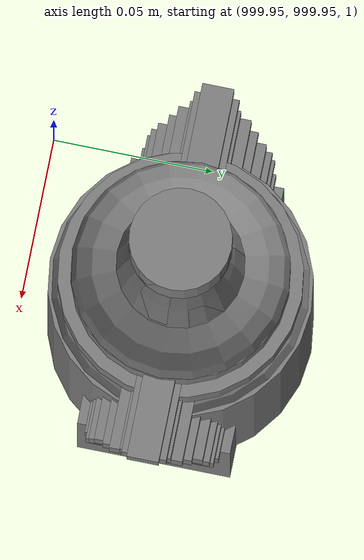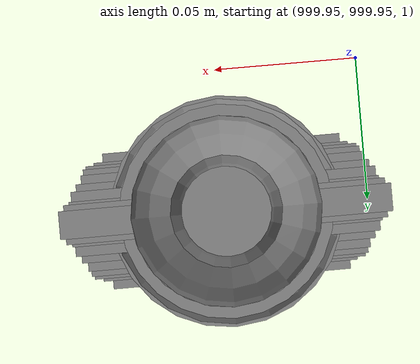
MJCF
<mujoco>
    <option gravity="0.000000000 0.000000000 -9.810000420" timestep="0.0166666" integrator="implicitfast" density="1.225" viscosity="1.8000001e-05" noslip_iterations="10" iterations="100" sdf_iterations="50">
        <flag multiccd="disable"/>
    </option>
    <size memory="1000M"/>
    <compiler coordinate="local"/>
    <worldbody>
        <light cutoff="30" pos="0 1 1" dir="0 -1 -2"/>
        <light cutoff="30" pos="0 -1 1" dir="0 1 -2"/>
        <body pos="-2.436573029 6.404376507 0.137849092" euler="0.000000000 0.000000000 0.000000000" name="openloong_gripper_2f85_fix_base_usda_shoppingtrolley_01">
            <geom contype="1" conaffinity="1" density="1000" type="box" material="" rgba="0.500000000 0.500000000 0.500000000 1.000000000" solimp="0.899999976 0.949999988 0.001000000" friction="1.000000000 0.005000000 0.000100000" solref="0.020000000 1.000000000" margin="0" condim="3" group="0" pos="-0.126757339 -0.182533979 0.598989725" quat="0.996607184 0.055331606 -0.059003651 -0.015205891" size="0.013499999 0.287999988 0.053999998" name="openloong_gripper_2f85_fix_base_usda_geom_46D16EB1_93FB_49AE_8E5E_1A4C25AC6C77"/>
            <geom contype="1" conaffinity="1" density="1000" type="box" material="" rgba="0.500000000 0.500000000 0.500000000 1.000000000" solimp="0.899999976 0.949999988 0.001000000" friction="1.000000000 0.005000000 0.000100000" solref="0.020000000 1.000000000" margin="0" condim="3" group="0" pos="-0.000005364 0.100332208 0.734785020" quat="0.999668717 0.025737956 -0.000000010 0.000000000" size="0.135000005 0.019800000 0.152999997" name="openloong_gripper_2f85_fix_base_usda_geom_524FBCDE_560E_4804_B392_352E8D7C707F"/>
            <geom contype="1" conaffinity="1" density="1000" type="box" material="" rgba="0.500000000 0.500000000 0.500000000 1.000000000" solimp="0.899999976 0.949999988 0.001000000" friction="1.000000000 0.005000000 0.000100000" solref="0.020000000 1.000000000" margin="0" condim="3" group="0" pos="-0.142927840 -0.199506134 0.784674108" quat="0.998421252 0.016904408 -0.027109101 -0.046199299" size="0.013499999 0.305999994 0.063000001" name="openloong_gripper_2f85_fix_base_usda_geom_DF9908F5_74A2_47A6_8380_679E0AB922F9"/>
            <geom contype="1" conaffinity="1" density="1000" type="box" material="" rgba="0.500000000 0.500000000 0.500000000 1.000000000" solimp="0.899999976 0.949999988 0.001000000" friction="1.000000000 0.005000000 0.000100000" solref="0.020000000 1.000000000" margin="0" condim="3" group="0" pos="-0.000006008 -0.484932661 0.670727849" quat="0.997585475 0.069449045 -0.000000004 -0.000000089" size="0.179999992 0.013499999 0.170999989" name="openloong_gripper_2f85_fix_base_usda_geom_F7B6F278_06EE_42C2_952E_F277BCB06C79"/>
            <geom contype="1" conaffinity="1" density="1000" type="box" material="" rgba="0.500000000 0.500000000 0.500000000 1.000000000" solimp="0.899999976 0.949999988 0.001000000" friction="1.000000000 0.005000000 0.000100000" solref="0.020000000 1.000000000" margin="0" condim="3" group="0" pos="-0.000004721 -0.174527690 0.560063601" quat="0.996704638 0.081116498 -0.000000004 0.000000000" size="0.126000002 0.287999988 0.009000000" name="openloong_gripper_2f85_fix_base_usda_geom_6FA744DD_60E8_44DD_8321_F38DB1F59B6A"/>
            <geom contype="1" conaffinity="1" density="1000" type="box" material="" rgba="0.500000000 0.500000000 0.500000000 1.000000000" solimp="0.899999976 0.949999988 0.001000000" friction="1.000000000 0.005000000 0.000100000" solref="0.020000000 1.000000000" margin="0" condim="3" group="0" pos="-0.012634277 -0.174527690 -0.088243507" quat="1.000000000 0.000000000 -0.000000004 0.000000000" size="0.135000005 0.287999988 0.044999998" name="openloong_gripper_2f85_fix_base_usda_geom_F6510746_4DE4_4439_AD55_E7F5CE170D08"/>
            <geom contype="1" conaffinity="1" density="1000" type="box" material="" rgba="0.500000000 0.500000000 0.500000000 1.000000000" solimp="0.899999976 0.949999988 0.001000000" friction="1.000000000 0.005000000 0.000100000" solref="0.020000000 1.000000000" margin="0" condim="3" group="0" pos="0.131482959 -0.182533979 0.598989725" quat="0.996607125 0.055331629 0.059003670 0.015205893" size="0.013499999 0.287999988 0.053999998" name="openloong_gripper_2f85_fix_base_usda_geom_F594637D_A691_4813_B898_9CCA7721C8FC"/>
            <geom contype="1" conaffinity="1" density="1000" type="box" material="" rgba="0.500000000 0.500000000 0.500000000 1.000000000" solimp="0.899999976 0.949999988 0.001000000" friction="1.000000000 0.005000000 0.000100000" solref="0.020000000 1.000000000" margin="0" condim="3" group="0" pos="0.148195267 -0.199506566 0.782808602" quat="0.998808920 0.017156634 0.026950166 0.036880098" size="0.013499999 0.305999994 0.063000001" name="openloong_gripper_2f85_fix_base_usda_geom_270C3E08_41C5_4289_9C49_74C981BF33E2"/>
            <geom contype="1" conaffinity="1" density="1000" type="box" material="" rgba="0.500000000 0.500000000 0.500000000 1.000000000" solimp="0.899999976 0.949999988 0.001000000" friction="1.000000000 0.005000000 0.000100000" solref="0.020000000 1.000000000" margin="0" condim="3" group="0" pos="0.103667587 0.233050480 0.912927270" quat="0.634205043 -0.622199059 -0.324503720 0.324576139" size="0.017999999 0.022499999 0.035999998" name="openloong_gripper_2f85_fix_base_usda_geom_D9748F4F_0FA5_4F77_9EA9_87379F3423B5"/>
            <geom contype="1" conaffinity="1" density="1000" type="box" material="" rgba="0.500000000 0.500000000 0.500000000 1.000000000" solimp="0.899999976 0.949999988 0.001000000" friction="1.000000000 0.005000000 0.000100000" solref="0.020000000 1.000000000" margin="0" condim="3" group="0" pos="-0.107458733 0.238907143 0.911498845" quat="0.634576976 0.622505128 -0.330067992 -0.317575932" size="0.017999999 0.022499999 0.035999998" name="openloong_gripper_2f85_fix_base_usda_geom_10344AC9_CDE7_47FF_BD77_B991C3D03310"/>
            <geom contype="1" conaffinity="1" density="1000" type="box" material="" rgba="0.500000000 0.500000000 0.500000000 1.000000000" solimp="0.899999976 0.949999988 0.001000000" friction="1.000000000 0.005000000 0.000100000" solref="0.020000000 1.000000000" margin="0" condim="3" group="0" pos="-0.169898406 -0.178061336 0.864131629" quat="0.916343808 -0.400392294 -0.000000045 0.000000030" size="0.017999999 0.022499999 0.089999996" name="openloong_gripper_2f85_fix_base_usda_geom_3B87FDC3_FFBA_4753_9402_69419415D4CB"/>
            <geom contype="1" conaffinity="1" density="1000" type="box" material="" rgba="0.500000000 0.500000000 0.500000000 1.000000000" solimp="0.899999976 0.949999988 0.001000000" friction="1.000000000 0.005000000 0.000100000" solref="0.020000000 1.000000000" margin="0" condim="3" group="0" pos="0.169898629 -0.178061336 0.864131629" quat="0.916343808 -0.400392294 -0.000000045 0.000000030" size="0.017999999 0.022499999 0.089999996" name="openloong_gripper_2f85_fix_base_usda_geom_CB3D1A21_31F5_44AD_B8C8_054669FEE98A"/>
            <geom contype="1" conaffinity="1" density="1000" type="box" material="" rgba="0.500000000 0.500000000 0.500000000 1.000000000" solimp="0.899999976 0.949999988 0.001000000" friction="1.000000000 0.005000000 0.000100000" solref="0.020000000 1.000000000" margin="0" condim="3" group="0" pos="-0.005004787 0.248085022 0.912686050" quat="1.000000000 0.000000000 0.000000000 0.000000000" size="0.107999995 0.022499999 0.022499999" name="openloong_gripper_2f85_fix_base_usda_geom_F93C354B_DAF6_4232_90EF_BC6E177CCA6E"/>
            <geom contype="1" conaffinity="1" density="1000" type="box" material="" rgba="0.500000000 0.500000000 0.500000000 1.000000000" solimp="0.899999976 0.949999988 0.001000000" friction="1.000000000 0.005000000 0.000100000" solref="0.020000000 1.000000000" margin="0" condim="3" group="0" pos="-0.169898406 -0.043119621 0.915120542" quat="0.687021017 0.726584017 -0.005590606 -0.006832919" size="0.017999999 0.022499999 0.089999996" name="openloong_gripper_2f85_fix_base_usda_geom_DC9363FB_9873_4A9B_8652_A96B5A3E0897"/>
            <geom contype="1" conaffinity="1" density="1000" type="box" material="" rgba="0.500000000 0.500000000 0.500000000 1.000000000" solimp="0.899999976 0.949999988 0.001000000" friction="1.000000000 0.005000000 0.000100000" solref="0.020000000 1.000000000" margin="0" condim="3" group="0" pos="0.141839072 -0.191051379 0.702451229" quat="0.997147262 0.056065105 0.045779929 0.021407485" size="0.013499999 0.287999988 0.053999998" name="openloong_gripper_2f85_fix_base_usda_geom_D99F0B65_FEAD_4083_89EF_5E6A003AC6D9"/>
            <geom contype="1" conaffinity="1" density="1000" type="box" material="" rgba="0.500000000 0.500000000 0.500000000 1.000000000" solimp="0.899999976 0.949999988 0.001000000" friction="1.000000000 0.005000000 0.000100000" solref="0.020000000 1.000000000" margin="0" condim="3" group="0" pos="0.160832971 0.103427693 0.910528183" quat="0.711112797 -0.700149298 -0.042821646 0.047705106" size="0.017999999 0.022499999 0.071999997" name="openloong_gripper_2f85_fix_base_usda_geom_3964E6F4_42E7_46FE_B71A_F230216512FC"/>
            <geom contype="1" conaffinity="1" density="1000" type="box" material="" rgba="0.500000000 0.500000000 0.500000000 1.000000000" solimp="0.899999976 0.949999988 0.001000000" friction="1.000000000 0.005000000 0.000100000" solref="0.020000000 1.000000000" margin="0" condim="3" group="0" pos="-0.134013891 0.200098798 0.912192523" quat="0.694057047 0.679413557 -0.172947660 -0.163618833" size="0.017999999 0.022499999 0.035999998" name="openloong_gripper_2f85_fix_base_usda_geom_285BF173_D422_465D_A477_8A4C54F76A63"/>
            <geom contype="1" conaffinity="1" density="1000" type="box" material="" rgba="0.500000000 0.500000000 0.500000000 1.000000000" solimp="0.899999976 0.949999988 0.001000000" friction="1.000000000 0.005000000 0.000100000" solref="0.020000000 1.000000000" margin="0" condim="3" group="0" pos="-0.160832763 0.103427693 0.910528183" quat="0.711469591 0.699786782 -0.048386075 -0.042050660" size="0.017999999 0.022499999 0.071999997" name="openloong_gripper_2f85_fix_base_usda_geom_EF06DB81_73B6_4037_BC28_6F33DFDF8B8D"/>
            <geom contype="1" conaffinity="1" density="1000" type="box" material="" rgba="0.500000000 0.500000000 0.500000000 1.000000000" solimp="0.899999976 0.949999988 0.001000000" friction="1.000000000 0.005000000 0.000100000" solref="0.020000000 1.000000000" margin="0" condim="3" group="0" pos="-0.135714188 -0.191051379 0.694841146" quat="0.997147322 0.056064609 -0.045779683 -0.021407485" size="0.013499999 0.287999988 0.053999998" name="openloong_gripper_2f85_fix_base_usda_geom_C8E06F6B_751E_46CB_9DCF_A9003BD0B389"/>
            <geom contype="1" conaffinity="1" density="1000" type="box" material="" rgba="0.500000000 0.500000000 0.500000000 1.000000000" solimp="0.899999976 0.949999988 0.001000000" friction="1.000000000 0.005000000 0.000100000" solref="0.020000000 1.000000000" margin="0" condim="3" group="0" pos="0.134013891 0.200098798 0.912192523" quat="0.692574680 -0.680924535 -0.166899428 0.169783980" size="0.017999999 0.022499999 0.035999998" name="openloong_gripper_2f85_fix_base_usda_geom_75E2116F_FC4A_46EC_9E95_C7648A142A9D"/>
            <geom contype="1" conaffinity="1" density="1000" type="box" material="" rgba="0.500000000 0.500000000 0.500000000 1.000000000" solimp="0.899999976 0.949999988 0.001000000" friction="1.000000000 0.005000000 0.000100000" solref="0.020000000 1.000000000" margin="0" condim="3" group="0" pos="0.169898629 -0.043119621 0.915120542" quat="0.687029123 -0.726576388 -0.006509603 0.005963952" size="0.017999999 0.022499999 0.089999996" name="openloong_gripper_2f85_fix_base_usda_geom_004B857A_134F_4303_B359_3D8AEB17F369"/>
            <freejoint name="openloong_gripper_2f85_fix_base_usda_shoppingtrolley_01_joint"/>
            <site size="0.005000000 0.005000000 0.005000000" rgba="0.500000000 0.500000000 0.500000000 1.000000000" pos="0.000000000 0.000000000 0.000000000" quat="1.000000000 0.000000000 0.000000000 0.000000000" group="0" type="sphere" name="openloong_gripper_2f85_fix_base_usda_shoppingtrolley_01"/>
        </body>
        <body pos="1000.000000000 1000.000000000 1.000000000" euler="0.000000000 0.000000000 0.000000000" name="openloong_gripper_2f85_fix_base_usda_can">
            <geom contype="1" conaffinity="1" density="1000" type="cylinder" material="" rgba="0.500000000 0.500000000 0.500000000 1.000000000" solimp="0.899999976 0.949999988 0.001000000" friction="1.000000000 0.005000000 0.000100000" solref="0.020000000 1.000000000" margin="0" condim="3" group="0" pos="0.000000000 0.000000000 0.079676986" quat="1.000000000 0.000000000 0.000000000 0.000000000" size="0.034000002 0.071999997 1.000000000" name="openloong_gripper_2f85_fix_base_usda_geom_EC5D4524_5183_4EC0_9EE1_5E32A12D0628"/>
            <geom contype="1" conaffinity="1" density="1000" type="ellipsoid" material="" rgba="0.500000000 0.500000000 0.500000000 1.000000000" solimp="0.899999976 0.949999988 0.001000000" friction="1.000000000 0.005000000 0.000100000" solref="0.020000000 1.000000000" margin="0" condim="3" group="0" pos="0.000000000 0.000000000 0.151854277" quat="1.000000000 0.000000000 0.000000000 0.000000000" size="0.034000002 0.034000002 0.020000000" name="openloong_gripper_2f85_fix_base_usda_geom_23331D79_182D_483F_AAC2_FA37F51F01B5"/>
            <geom contype="1" conaffinity="1" density="1000" type="box" material="" rgba="0.500000000 0.500000000 0.500000000 1.000000000" solimp="0.899999976 0.949999988 0.001000000" friction="1.000000000 0.005000000 0.000100000" solref="0.020000000 1.000000000" margin="0" condim="3" group="0" pos="0.000000000 0.000000000 0.004777670" quat="1.000000000 0.000000000 0.000000000 0.000000000" size="0.020000000 0.020000000 0.005000000" name="openloong_gripper_2f85_fix_base_usda_geom_7045AE4B_DD27_42C2_8F6F_16C4DB7E4CD8"/>
            <freejoint name="openloong_gripper_2f85_fix_base_usda_can_joint"/>
            <site size="0.005000000 0.005000000 0.005000000" rgba="0.500000000 0.500000000 0.500000000 1.000000000" pos="0.000000000 0.000000000 0.000000000" quat="1.000000000 0.000000000 0.000000000 0.000000000" group="0" type="sphere" name="openloong_gripper_2f85_fix_base_usda_cansite"/>
        </body>
        <body pos="1000.000000000 1000.000000000 1.000000000" euler="0.000000000 0.000000000 0.000000000" name="openloong_gripper_2f85_fix_base_usda_salt">
            <geom contype="1" conaffinity="1" density="1000" type="box" material="" rgba="0.500000000 0.500000000 0.500000000 1.000000000" solimp="0.899999976 0.949999988 0.001000000" friction="1.000000000 0.005000000 0.000100000" solref="0.020000000 1.000000000" margin="0" condim="3" group="0" pos="0.000305176 0.000000000 0.084862232" quat="1.000000000 0.000000000 0.000000000 0.000000000" size="0.048999999 0.018999999 0.005000000" name="openloong_gripper_2f85_fix_base_usda_geom_ADEA2C03_7204_4DE0_AE9F_312B4DA4EDA4"/>
            <geom contype="1" conaffinity="1" density="1000" type="box" material="" rgba="0.500000000 0.500000000 0.500000000 1.000000000" solimp="0.899999976 0.949999988 0.001000000" friction="1.000000000 0.005000000 0.000100000" solref="0.020000000 1.000000000" margin="0" condim="3" group="0" pos="0.000305176 0.000000000 0.104564309" quat="1.000000000 0.000000000 0.000000000 0.000000000" size="0.052000001 0.014000000 0.005000000" name="openloong_gripper_2f85_fix_base_usda_geom_A71000A4_7573_4143_8A75_2D39030C0D69"/>
            <geom contype="1" conaffinity="1" density="1000" type="box" material="" rgba="0.500000000 0.500000000 0.500000000 1.000000000" solimp="0.899999976 0.949999988 0.001000000" friction="1.000000000 0.005000000 0.000100000" solref="0.020000000 1.000000000" margin="0" condim="3" group="0" pos="0.000305176 0.000000000 0.114487171" quat="1.000000000 0.000000000 0.000000000 0.000000000" size="0.054000001 0.011500000 0.005000000" name="openloong_gripper_2f85_fix_base_usda_geom_65B6B4B7_AFA2_4C8C_B65C_DDE40AA029A8"/>
            <geom contype="1" conaffinity="1" density="1000" type="box" material="" rgba="0.500000000 0.500000000 0.500000000 1.000000000" solimp="0.899999976 0.949999988 0.001000000" friction="1.000000000 0.005000000 0.000100000" solref="0.020000000 1.000000000" margin="0" condim="3" group="0" pos="0.000305176 0.000000000 0.075103164" quat="1.000000000 0.000000000 0.000000000 0.000000000" size="0.048000000 0.020000000 0.005000000" name="openloong_gripper_2f85_fix_base_usda_geom_931F70D5_F929_4EC4_A920_75E98B8160D0"/>
            <geom contype="1" conaffinity="1" density="1000" type="box" material="" rgba="0.500000000 0.500000000 0.500000000 1.000000000" solimp="0.899999976 0.949999988 0.001000000" friction="1.000000000 0.005000000 0.000100000" solref="0.020000000 1.000000000" margin="0" condim="3" group="0" pos="0.000305176 0.000000000 0.134892464" quat="1.000000000 0.000000000 0.000000000 0.000000000" size="0.057000000 0.007000000 0.005000000" name="openloong_gripper_2f85_fix_base_usda_geom_FA1344C2_072E_4F0F_A816_3096780FC007"/>
            <geom contype="1" conaffinity="1" density="1000" type="box" material="" rgba="0.500000000 0.500000000 0.500000000 1.000000000" solimp="0.899999976 0.949999988 0.001000000" friction="1.000000000 0.005000000 0.000100000" solref="0.020000000 1.000000000" margin="0" condim="3" group="0" pos="0.000305176 0.000000000 0.094920278" quat="1.000000000 0.000000000 0.000000000 0.000000000" size="0.050000001 0.017000001 0.005000000" name="openloong_gripper_2f85_fix_base_usda_geom_91D1D8CA_1541_4C10_ADC4_4817CF1880EA"/>
            <geom contype="1" conaffinity="1" density="1000" type="box" material="" rgba="0.500000000 0.500000000 0.500000000 1.000000000" solimp="0.899999976 0.949999988 0.001000000" friction="1.000000000 0.005000000 0.000100000" solref="0.020000000 1.000000000" margin="0" condim="3" group="0" pos="0.000305176 0.000000000 0.065204859" quat="1.000000000 0.000000000 0.000000000 0.000000000" size="0.045000002 0.021000000 0.005000000" name="openloong_gripper_2f85_fix_base_usda_geom_1DC09363_52B6_449E_910E_4FFEB2A0F8E7"/>
            <geom contype="1" conaffinity="1" density="1000" type="box" material="" rgba="0.500000000 0.500000000 0.500000000 1.000000000" solimp="0.899999976 0.949999988 0.001000000" friction="1.000000000 0.005000000 0.000100000" solref="0.020000000 1.000000000" margin="0" condim="3" group="0" pos="0.000305176 0.000000000 0.144135714" quat="1.000000000 0.000000000 0.000000000 0.000000000" size="0.059000000 0.005000000 0.004000000" name="openloong_gripper_2f85_fix_base_usda_geom_24A6C70C_8943_489C_BE2F_8CE5EF52DED9"/>
            <geom contype="1" conaffinity="1" density="1000" type="box" material="" rgba="0.500000000 0.500000000 0.500000000 1.000000000" solimp="0.899999976 0.949999988 0.001000000" friction="1.000000000 0.005000000 0.000100000" solref="0.020000000 1.000000000" margin="0" condim="3" group="0" pos="0.000000000 0.000000000 0.031593561" quat="1.000000000 0.000000000 0.000000000 0.000000000" size="0.041999999 0.024000000 0.029999999" name="openloong_gripper_2f85_fix_base_usda_geom_76502CFB_8113_451E_A5C0_AC36EF74EE5B"/>
            <geom contype="1" conaffinity="1" density="1000" type="box" material="" rgba="0.500000000 0.500000000 0.500000000 1.000000000" solimp="0.899999976 0.949999988 0.001000000" friction="1.000000000 0.005000000 0.000100000" solref="0.020000000 1.000000000" margin="0" condim="3" group="0" pos="0.000305176 0.000000000 0.124608755" quat="1.000000000 0.000000000 0.000000000 0.000000000" size="0.055000000 0.008000000 0.005000000" name="openloong_gripper_2f85_fix_base_usda_geom_23B49450_4B20_4F71_BD8B_78229644CC2C"/>
            <freejoint name="openloong_gripper_2f85_fix_base_usda_salt_joint"/>
            <site size="0.005000000 0.005000000 0.005000000" rgba="0.500000000 0.500000000 0.500000000 1.000000000" pos="0.000000000 0.000000000 0.000000000" quat="1.000000000 0.000000000 0.000000000 0.000000000" group="0" type="sphere" name="openloong_gripper_2f85_fix_base_usda_saltsite"/>
        </body>
        <body pos="-1.925213456 6.073964596 1.690697670" euler="-1.885598302 -54.620468140 -171.968566895" mocap="true" name="spotlight5_SpotLight"/>
        <body pos="-1.825461388 5.896390438 1.831195235" euler="-38.453552246 22.543159485 -105.044769287" mocap="true" name="spotlight2_SpotLight"/>
        <body pos="1000.000000000 1000.000000000 1.000000000" euler="0.000000000 0.000000000 0.000000000" name="openloong_gripper_2f85_fix_base_usda_bottle_red">
            <geom contype="1" conaffinity="1" density="1000" type="ellipsoid" material="" rgba="0.500000000 0.500000000 0.500000000 1.000000000" solimp="0.899999976 0.949999988 0.001000000" friction="1.000000000 0.005000000 0.000100000" solref="0.020000000 1.000000000" margin="0" condim="3" group="0" pos="0.000000000 0.000000000 0.144284487" quat="1.000000000 0.000000000 0.000000000 0.000000000" size="0.021000000 0.021000000 0.079999998" name="openloong_gripper_2f85_fix_base_usda_geom_10282EDF_2E75_484B_A9A6_85B90DB7A6AC"/>
            <geom contype="1" conaffinity="1" density="1000" type="cylinder" material="" rgba="0.500000000 0.500000000 0.500000000 1.000000000" solimp="0.899999976 0.949999988 0.001000000" friction="1.000000000 0.005000000 0.000100000" solref="0.020000000 1.000000000" margin="0" condim="3" group="0" pos="0.000000000 0.000000000 0.220618963" quat="1.000000000 0.000000000 0.000000000 0.000000000" size="0.016000001 0.010000000 1.000000000" name="openloong_gripper_2f85_fix_base_usda_geom_8FE1277B_E46D_4165_8006_4E803CF13357"/>
            <geom contype="1" conaffinity="1" density="1000" type="ellipsoid" material="" rgba="0.500000000 0.500000000 0.500000000 1.000000000" solimp="0.899999976 0.949999988 0.001000000" friction="1.000000000 0.005000000 0.000100000" solref="0.020000000 1.000000000" margin="0" condim="3" group="0" pos="0.000000000 0.000000000 0.118945479" quat="1.000000000 0.000000000 0.000000000 0.000000000" size="0.030999999 0.030999999 0.029999999" name="openloong_gripper_2f85_fix_base_usda_geom_68B1DC27_27D8_4084_9B68_56BC42C383AF"/>
            <geom contype="1" conaffinity="1" density="1000" type="box" material="" rgba="0.500000000 0.500000000 0.500000000 1.000000000" solimp="0.899999976 0.949999988 0.001000000" friction="1.000000000 0.005000000 0.000100000" solref="0.020000000 1.000000000" margin="0" condim="3" group="0" pos="0.000000000 0.000000000 0.002189159" quat="1.000000000 0.000000000 0.000000000 0.000000000" size="0.020000000 0.020000000 0.003000000" name="openloong_gripper_2f85_fix_base_usda_geom_ED862F7C_F3CE_45DC_A11C_56D9A37D2087"/>
            <geom contype="1" conaffinity="1" density="1000" type="cylinder" material="" rgba="0.500000000 0.500000000 0.500000000 1.000000000" solimp="0.899999976 0.949999988 0.001000000" friction="1.000000000 0.005000000 0.000100000" solref="0.020000000 1.000000000" margin="0" condim="3" group="0" pos="0.000000000 -0.000366211 0.060884237" quat="1.000000000 0.000000000 0.000000000 0.000000000" size="0.030999999 0.057999998 1.000000000" name="openloong_gripper_2f85_fix_base_usda_geom_D52D6923_0FB5_4769_8282_327925F14425"/>
            <freejoint name="openloong_gripper_2f85_fix_base_usda_bottle_red_joint"/>
            <site size="0.005000000 0.005000000 0.005000000" rgba="0.500000000 0.500000000 0.500000000 1.000000000" pos="0.000000000 0.000000000 0.000000000" quat="0.999961913 0.008726535 0.000000000 0.000000000" group="0" type="sphere" name="openloong_gripper_2f85_fix_base_usda_bottle_redsite"/>
        </body>
        <body pos="-1.779756784 6.167755604 1.763255596" euler="-105.682731628 -15.979977608 170.721282959" mocap="true" name="spotlight6_SpotLight"/>
        <body pos="1000.000000000 1000.000000000 1.000000000" euler="0.000000000 0.000000000 0.000000000" name="openloong_gripper_2f85_fix_base_usda_bottle_blue">
            <geom contype="1" conaffinity="1" density="1000" type="ellipsoid" material="" rgba="0.500000000 0.500000000 0.500000000 1.000000000" solimp="0.899999976 0.949999988 0.001000000" friction="1.000000000 0.005000000 0.000100000" solref="0.020000000 1.000000000" margin="0" condim="3" group="0" pos="0.000000000 0.000000000 0.118920922" quat="1.000000000 0.000000000 0.000000000 0.000000000" size="0.030999999 0.030999999 0.029999999" name="openloong_gripper_2f85_fix_base_usda_geom_A0C5EC13_94A4_4557_85FD_B903DAF980C6"/>
            <geom contype="1" conaffinity="1" density="1000" type="box" material="" rgba="0.500000000 0.500000000 0.500000000 1.000000000" solimp="0.899999976 0.949999988 0.001000000" friction="1.000000000 0.005000000 0.000100000" solref="0.020000000 1.000000000" margin="0" condim="3" group="0" pos="0.000000000 0.000000000 0.002164602" quat="1.000000000 0.000000000 0.000000000 0.000000000" size="0.020000000 0.020000000 0.003000000" name="openloong_gripper_2f85_fix_base_usda_geom_76C2BC28_9343_4866_B055_BC99DA159A94"/>
            <geom contype="1" conaffinity="1" density="1000" type="cylinder" material="" rgba="0.500000000 0.500000000 0.500000000 1.000000000" solimp="0.899999976 0.949999988 0.001000000" friction="1.000000000 0.005000000 0.000100000" solref="0.020000000 1.000000000" margin="0" condim="3" group="0" pos="0.000000000 -0.000366211 0.060859680" quat="1.000000000 0.000000000 0.000000000 0.000000000" size="0.030999999 0.057999998 1.000000000" name="openloong_gripper_2f85_fix_base_usda_geom_8D9BC1BA_4E01_42C3_B73F_3A327D56C693"/>
            <geom contype="1" conaffinity="1" density="1000" type="cylinder" material="" rgba="0.500000000 0.500000000 0.500000000 1.000000000" solimp="0.899999976 0.949999988 0.001000000" friction="1.000000000 0.005000000 0.000100000" solref="0.020000000 1.000000000" margin="0" condim="3" group="0" pos="0.000000000 0.000000000 0.220594406" quat="1.000000000 0.000000000 0.000000000 0.000000000" size="0.016000001 0.010000000 1.000000000" name="openloong_gripper_2f85_fix_base_usda_geom_5E59B3AE_A7F7_4227_B786_2290CD91A0D9"/>
            <geom contype="1" conaffinity="1" density="1000" type="ellipsoid" material="" rgba="0.500000000 0.500000000 0.500000000 1.000000000" solimp="0.899999976 0.949999988 0.001000000" friction="1.000000000 0.005000000 0.000100000" solref="0.020000000 1.000000000" margin="0" condim="3" group="0" pos="0.000000000 0.000000000 0.144259930" quat="1.000000000 0.000000000 0.000000000 0.000000000" size="0.021000000 0.021000000 0.079999998" name="openloong_gripper_2f85_fix_base_usda_geom_17956BE9_E225_4BEA_AB35_DABB866C372B"/>
            <freejoint name="openloong_gripper_2f85_fix_base_usda_bottle_blue_joint"/>
            <site size="0.005000000 0.005000000 0.005000000" rgba="0.500000000 0.500000000 0.500000000 1.000000000" pos="0.000000000 0.000000000 0.000000000" quat="0.999961913 0.008726535 0.000000000 0.000000000" group="0" type="sphere" name="openloong_gripper_2f85_fix_base_usda_bottle_bluesite"/>
        </body>
        <body pos="1000.000000000 1000.000000000 1.000000000" euler="0.000000000 0.000000000 0.000000000" name="openloong_gripper_2f85_fix_base_usda_jar_01">
            <geom contype="1" conaffinity="1" density="1000" type="box" material="" rgba="0.500000000 0.500000000 0.500000000 1.000000000" solimp="0.899999976 0.949999988 0.001000000" friction="1.000000000 0.005000000 0.000100000" solref="0.020000000 1.000000000" margin="0" condim="3" group="0" pos="0.000000000 0.000000000 0.006158113" quat="1.000000000 0.000000000 0.000000000 0.000000000" size="0.020000000 0.020000000 0.005000000" name="openloong_gripper_2f85_fix_base_usda_geom_4AFE11A5_0709_490C_9474_25ABA384D79C"/>
            <geom contype="1" conaffinity="1" density="1000" type="cylinder" material="" rgba="0.500000000 0.500000000 0.500000000 1.000000000" solimp="0.899999976 0.949999988 0.001000000" friction="1.000000000 0.005000000 0.000100000" solref="0.020000000 1.000000000" margin="0" condim="3" group="0" pos="0.000000000 0.000000000 0.062744498" quat="1.000000000 0.000000000 0.000000000 0.000000000" size="0.041000001 0.052999999 1.000000000" name="openloong_gripper_2f85_fix_base_usda_geom_807781F6_EF75_4C4A_B1B2_14792B939BDB"/>
            <geom contype="1" conaffinity="1" density="1000" type="ellipsoid" material="" rgba="0.500000000 0.500000000 0.500000000 1.000000000" solimp="0.899999976 0.949999988 0.001000000" friction="1.000000000 0.005000000 0.000100000" solref="0.020000000 1.000000000" margin="0" condim="3" group="0" pos="0.000000000 0.000000000 0.122252703" quat="1.000000000 0.000000000 0.000000000 0.000000000" size="0.035999998 0.035999998 0.010000000" name="openloong_gripper_2f85_fix_base_usda_geom_AD226DFD_1A75_428F_95A1_B1CCDEFED536"/>
            <geom contype="1" conaffinity="1" density="1000" type="cylinder" material="" rgba="0.500000000 0.500000000 0.500000000 1.000000000" solimp="0.899999976 0.949999988 0.001000000" friction="1.000000000 0.005000000 0.000100000" solref="0.020000000 1.000000000" margin="0" condim="3" group="0" pos="0.000000000 0.000000000 0.015747190" quat="1.000000000 0.000000000 0.000000000 0.000000000" size="0.035000000 0.010000000 1.000000000" name="openloong_gripper_2f85_fix_base_usda_geom_FA2F3061_19E5_4FA4_AD9D_CC2FBD72D9EB"/>
            <geom contype="1" conaffinity="1" density="1000" type="ellipsoid" material="" rgba="0.500000000 0.500000000 0.500000000 1.000000000" solimp="0.899999976 0.949999988 0.001000000" friction="1.000000000 0.005000000 0.000100000" solref="0.020000000 1.000000000" margin="0" condim="3" group="0" pos="0.000000000 0.000000000 0.115815401" quat="1.000000000 0.000000000 0.000000000 0.000000000" size="0.039999999 0.039999999 0.010000000" name="openloong_gripper_2f85_fix_base_usda_geom_58C39FB8_EA46_4D85_BCAF_A7E2857D4510"/>
            <geom contype="1" conaffinity="1" density="1000" type="cylinder" material="" rgba="0.500000000 0.500000000 0.500000000 1.000000000" solimp="0.899999976 0.949999988 0.001000000" friction="1.000000000 0.005000000 0.000100000" solref="0.020000000 1.000000000" margin="0" condim="3" group="0" pos="0.000000000 0.000000000 0.133183479" quat="1.000000000 0.000000000 0.000000000 0.000000000" size="0.037999999 0.006500000 1.000000000" name="openloong_gripper_2f85_fix_base_usda_geom_5E95369B_0651_41F3_B04A_9457D3105779"/>
            <freejoint name="openloong_gripper_2f85_fix_base_usda_jar_01_joint"/>
            <site size="0.005000000 0.005000000 0.005000000" rgba="0.500000000 0.500000000 0.500000000 1.000000000" pos="0.000000000 0.000000000 0.000000000" quat="1.000000000 0.000000000 0.000000000 0.000000000" group="0" type="sphere" name="openloong_gripper_2f85_fix_base_usda_jar_01site"/>
        </body>
        <body pos="0.000000000 0.000000000 0.000000000" euler="0.000000000 0.000000000 0.000000000" name=" Static Objects_ Static Objects">
            <geom contype="1" conaffinity="1" density="1000" type="box" material="" rgba="0.500000000 0.500000000 0.500000000 1.000000000" solimp="0.899999976 0.949999988 0.001000000" friction="1.000000000 0.005000000 0.000100000" solref="0.020000000 1.000000000" margin="0" condim="3" group="0" pos="-3.101639986 6.150595188 1.018643856" quat="1.000000000 0.000000000 0.000000000 0.000000000" size="0.050000001 0.579999983 1.019999981" name=" Static Objects_geom_8B2930FE_9EC1_488E_A613_E84FC8F4B684"/>
            <geom contype="1" conaffinity="1" density="1000" type="box" material="" rgba="0.500000000 0.500000000 0.500000000 1.000000000" solimp="0.899999976 0.949999988 0.001000000" friction="1.000000000 0.005000000 0.000100000" solref="0.020000000 1.000000000" margin="0" condim="3" group="0" pos="-2.825197220 6.153595448 1.115278244" quat="0.707107067 0.000000000 0.000000000 0.707106471" size="0.550000012 0.239999995 0.025000000" name=" Static Objects_geom_BABB340A_D0F2_403D_A4EC_DF50E2B46506"/>
            <geom contype="1" conaffinity="1" density="1000" type="box" material="" rgba="0.500000000 0.500000000 0.500000000 1.000000000" solimp="0.899999976 0.949999988 0.001000000" friction="1.000000000 0.005000000 0.000100000" solref="0.020000000 1.000000000" margin="0" condim="3" group="0" pos="-2.825197220 6.153595448 0.097434282" quat="0.707107067 0.000000000 0.000000000 0.707106471" size="0.550000012 0.239999995 0.098999999" name=" Static Objects_geom_A700844B_85F5_4D7F_A07F_77F8039AB93B"/>
            <geom contype="1" conaffinity="1" density="1000" type="box" material="" rgba="0.500000000 0.500000000 0.500000000 1.000000000" solimp="0.899999976 0.949999988 0.001000000" friction="1.000000000 0.005000000 0.000100000" solref="0.020000000 1.000000000" margin="0" condim="3" group="0" pos="-6.293097973 6.153595448 1.114443064" quat="0.707107067 0.000000000 0.000000000 0.707106471" size="0.529999971 3.134999990 0.025000000" name=" Static Objects_geom_620CF0FB_5519_4387_9023_DAD29F33A4F1"/>
            <geom contype="1" conaffinity="1" density="1000" type="box" material="" rgba="0.500000000 0.500000000 0.500000000 1.000000000" solimp="0.899999976 0.949999988 0.001000000" friction="1.000000000 0.005000000 0.000100000" solref="0.020000000 1.000000000" margin="0" condim="3" group="0" pos="-2.825197220 6.153595448 1.563861728" quat="0.707107067 0.000000000 0.000000000 0.707106471" size="0.550000012 0.239999995 0.025000000" name=" Static Objects_geom_0B01EEC6_4824_4335_9A27_471DEB9BAE9D"/>
            <geom contype="1" conaffinity="1" density="1000" type="box" material="" rgba="0.500000000 0.500000000 0.500000000 1.000000000" solimp="0.899999976 0.949999988 0.001000000" friction="1.000000000 0.005000000 0.000100000" solref="0.020000000 1.000000000" margin="0" condim="3" group="0" pos="-6.311686516 6.153595448 1.018643856" quat="0.707107067 0.000000000 0.000000000 0.707106471" size="0.050000001 3.150000095 1.019999981" name=" Static Objects_geom_1BD887DE_B576_4580_BB6A_DF0E03455CD3"/>
            <geom contype="1" conaffinity="1" density="1000" type="box" material="" rgba="0.500000000 0.500000000 0.500000000 1.000000000" solimp="0.899999976 0.949999988 0.001000000" friction="1.000000000 0.005000000 0.000100000" solref="0.020000000 1.000000000" margin="0" condim="3" group="0" pos="-6.286010742 6.153595448 0.096129179" quat="0.707107067 0.000000000 0.000000000 0.707106471" size="0.529999971 3.134999990 0.098999999" name=" Static Objects_geom_28294658_4AC4_4EA1_B980_90ACE26EA03C"/>
            <geom contype="1" conaffinity="1" density="1000" type="box" material="" rgba="0.500000000 0.500000000 0.500000000 1.000000000" solimp="0.899999976 0.949999988 0.001000000" friction="1.000000000 0.005000000 0.000100000" solref="0.020000000 1.000000000" margin="0" condim="3" group="0" pos="-2.825197220 6.153595448 0.629031777" quat="0.707107067 0.000000000 0.000000000 0.707106471" size="0.550000012 0.239999995 0.025000000" name=" Static Objects_geom_00EACBF0_FB27_47A5_B5C8_73FB792E12D3"/>
            <geom contype="1" conaffinity="1" density="1000" type="box" material="" rgba="0.500000000 0.500000000 0.500000000 1.000000000" solimp="0.899999976 0.949999988 0.001000000" friction="1.000000000 0.005000000 0.000100000" solref="0.020000000 1.000000000" margin="0" condim="3" group="0" pos="-6.286010742 6.153595448 1.563861728" quat="0.707107067 0.000000000 0.000000000 0.707106471" size="0.529999971 3.134999990 0.025000000" name=" Static Objects_geom_24F49729_573A_4596_BBBC_7202A2199852"/>
            <geom contype="1" conaffinity="1" density="1000" type="box" material="" rgba="0.500000000 0.500000000 0.500000000 1.000000000" solimp="0.899999976 0.949999988 0.001000000" friction="1.000000000 0.005000000 0.000100000" solref="0.020000000 1.000000000" margin="0" condim="3" group="0" pos="-6.286010742 6.153595448 0.629031777" quat="0.707107067 0.000000000 0.000000000 0.707106471" size="0.529999971 3.134999990 0.025000000" name=" Static Objects_geom_BB3D3C7C_D1A8_429C_A81D_794C8DB0A026"/>
            <geom contype="1" conaffinity="1" density="1000" type="box" material="" rgba="0.500000000 0.500000000 0.500000000 1.000000000" solimp="0.899999976 0.949999988 0.001000000" friction="1.000000000 0.005000000 0.000100000" solref="0.020000000 1.000000000" margin="0" condim="3" group="0" pos="-3.157672644 6.136868477 1.348373055" quat="1.000000000 0.000000000 0.000000000 0.000000000" size="0.200000003 0.519999981 0.300000012" name=" Static Objects_geom_4E126F3B_7F24_45BE_BA79_C3ABA8E72AF3"/>
            <geom contype="1" conaffinity="1" density="1000" type="box" material="" rgba="0.500000000 0.500000000 0.500000000 1.000000000" solimp="0.899999976 0.949999988 0.001000000" friction="1.000000000 0.005000000 0.000100000" solref="0.020000000 1.000000000" margin="0" condim="3" group="0" pos="-7.719123363 2.867671013 1.173410416" quat="1.000000000 0.000000000 0.000000000 0.000000000" size="0.250000000 0.250000000 0.079999998" name=" Static Objects_geom_7264D918_0356_4D98_865B_D8F8B6BAB3CE"/>
            <geom contype="1" conaffinity="1" density="1000" type="box" material="" rgba="0.500000000 0.500000000 0.500000000 1.000000000" solimp="0.899999976 0.949999988 0.001000000" friction="1.000000000 0.005000000 0.000100000" solref="0.020000000 1.000000000" margin="0" condim="3" group="0" pos="-7.408766270 3.088089943 1.776644945" quat="0.928051054 0.000000000 0.000000000 0.372453064" size="0.050000001 0.100000001 0.050000001" name=" Static Objects_geom_270D9FB1_F21E_4672_A838_B52E83F23FB2"/>
            <geom contype="1" conaffinity="1" density="1000" type="box" material="" rgba="0.500000000 0.500000000 0.500000000 1.000000000" solimp="0.899999976 0.949999988 0.001000000" friction="1.000000000 0.005000000 0.000100000" solref="0.020000000 1.000000000" margin="0" condim="3" group="0" pos="-7.719123363 2.958004713 1.530241251" quat="1.000000000 0.000000000 0.000000000 0.000000000" size="0.250000000 0.159999996 0.280000001" name=" Static Objects_geom_AAAD2077_1326_4433_9954_1F8F9A255113"/>
            <geom contype="1" conaffinity="1" density="1000" type="cylinder" material="" rgba="0.500000000 0.500000000 0.500000000 1.000000000" solimp="0.899999976 0.949999988 0.001000000" friction="1.000000000 0.005000000 0.000100000" solref="0.020000000 1.000000000" margin="0" condim="3" group="0" pos="-7.427312374 3.069516420 1.502544641" quat="0.928051054 0.000000000 0.000000000 0.372453064" size="0.015000000 0.230000004 0.100000001" name=" Static Objects_geom_0FD85986_5E51_45A4_B674_CE575310D39D"/>
            <geom contype="1" conaffinity="1" density="1000" type="box" material="" rgba="0.500000000 0.500000000 0.500000000 1.000000000" solimp="0.899999976 0.949999988 0.001000000" friction="1.000000000 0.005000000 0.000100000" solref="0.020000000 1.000000000" margin="0" condim="3" group="0" pos="-7.437745571 3.067511320 1.289965630" quat="1.000000000 0.000000000 0.000000000 0.000000000" size="0.029999999 0.020000000 0.020000000" name=" Static Objects_geom_615BC24A_CC15_430F_9DA2_03DA897E9BF2"/>
            <geom contype="1" conaffinity="1" density="1000" type="box" material="" rgba="0.500000000 0.500000000 0.500000000 1.000000000" solimp="0.899999976 0.949999988 0.001000000" friction="1.000000000 0.005000000 0.000100000" solref="0.020000000 1.000000000" margin="0" condim="3" group="0" pos="-9.058088303 6.434794426 1.209077358" quat="1.000000000 0.000000000 0.000000000 0.000000000" size="0.250000000 0.100000001 0.070000000" name=" Static Objects_geom_ABA17C3D_23B0_40DB_9F94_C4267635F5A0"/>
            <geom contype="1" conaffinity="1" density="1000" type="box" material="" rgba="0.500000000 0.500000000 0.500000000 1.000000000" solimp="0.899999976 0.949999988 0.001000000" friction="1.000000000 0.005000000 0.000100000" solref="0.020000000 1.000000000" margin="0" condim="3" group="0" pos="-7.886891365 6.459744930 0.352518857" quat="1.000000000 0.000000000 0.000000000 0.000000000" size="1.500000000 0.200000003 0.150000006" name=" Static Objects_geom_1A059D74_734D_4CD4_94CD_6714973DB524"/>
            <geom contype="1" conaffinity="1" density="1000" type="box" material="" rgba="0.500000000 0.500000000 0.500000000 1.000000000" solimp="0.899999976 0.949999988 0.001000000" friction="1.000000000 0.005000000 0.000100000" solref="0.020000000 1.000000000" margin="0" condim="3" group="0" pos="-9.237723351 6.464855671 1.209077358" quat="1.000000000 0.000000000 0.000000000 0.000000000" size="0.100000001 0.100000001 0.070000000" name=" Static Objects_geom_84888CD2_798A_4BAE_B37E_2B2F5F2D0F0B"/>
            <geom contype="1" conaffinity="1" density="1000" type="box" material="" rgba="0.500000000 0.500000000 0.500000000 1.000000000" solimp="0.899999976 0.949999988 0.001000000" friction="1.000000000 0.005000000 0.000100000" solref="0.020000000 1.000000000" margin="0" condim="3" group="0" pos="-6.924745083 6.362090111 1.214329123" quat="1.000000000 0.000000000 0.000000000 0.000000000" size="0.200000003 0.100000001 0.075000003" name=" Static Objects_geom_B018CFB3_D2DD_41B6_BA50_972DA8C9C078"/>
            <geom contype="1" conaffinity="1" density="1000" type="box" material="" rgba="0.500000000 0.500000000 0.500000000 1.000000000" solimp="0.899999976 0.949999988 0.001000000" friction="1.000000000 0.005000000 0.000100000" solref="0.020000000 1.000000000" margin="0" condim="3" group="0" pos="-4.407354832 6.459744930 1.292199373" quat="1.000000000 0.000000000 0.000000000 0.000000000" size="1.240000010 0.200000003 0.150000006" name=" Static Objects_geom_5D4E4024_B310_487D_B9B4_AF2ED0ACD01A"/>
            <geom contype="1" conaffinity="1" density="1000" type="box" material="" rgba="0.500000000 0.500000000 0.500000000 1.000000000" solimp="0.899999976 0.949999988 0.001000000" friction="1.000000000 0.005000000 0.000100000" solref="0.020000000 1.000000000" margin="0" condim="3" group="0" pos="-5.611940861 6.318420410 0.350975692" quat="1.000000000 0.000000000 0.000000000 0.000000000" size="0.699999988 0.100000001 0.150000006" name=" Static Objects_geom_0FAB2E4D_E3DF_43CA_8A35_04649B5F5205"/>
            <geom contype="1" conaffinity="1" density="1000" type="box" material="" rgba="0.500000000 0.500000000 0.500000000 1.000000000" solimp="0.899999976 0.949999988 0.001000000" friction="1.000000000 0.005000000 0.000100000" solref="0.020000000 1.000000000" margin="0" condim="3" group="0" pos="-6.300771236 6.459744930 1.744376063" quat="1.000000000 0.000000000 0.000000000 0.000000000" size="3.000000000 0.200000003 0.150000006" name=" Static Objects_geom_674A2A2C_A1D9_46F3_9F36_7C4C887EDFAE"/>
            <geom contype="1" conaffinity="1" density="1000" type="box" material="" rgba="0.500000000 0.500000000 0.500000000 1.000000000" solimp="0.899999976 0.949999988 0.001000000" friction="1.000000000 0.005000000 0.000100000" solref="0.020000000 1.000000000" margin="0" condim="3" group="0" pos="-8.844120979 6.464855671 1.209077358" quat="1.000000000 0.000000000 0.000000000 0.000000000" size="0.100000001 0.100000001 0.070000000" name=" Static Objects_geom_073A2DCB_7D49_4D1E_863C_5CEFA0E35C24"/>
            <geom contype="1" conaffinity="1" density="1000" type="box" material="" rgba="0.500000000 0.500000000 0.500000000 1.000000000" solimp="0.899999976 0.949999988 0.001000000" friction="1.000000000 0.005000000 0.000100000" solref="0.020000000 1.000000000" margin="0" condim="3" group="0" pos="-6.824534416 6.447464466 1.212718010" quat="1.000000000 0.000000000 0.000000000 0.000000000" size="0.100000001 0.100000001 0.075000003" name=" Static Objects_geom_4956B845_B0E9_4717_A01D_07937CE7FC2F"/>
            <geom contype="1" conaffinity="1" density="1000" type="box" material="" rgba="0.500000000 0.500000000 0.500000000 1.000000000" solimp="0.899999976 0.949999988 0.001000000" friction="1.000000000 0.005000000 0.000100000" solref="0.020000000 1.000000000" margin="0" condim="3" group="0" pos="-6.751636982 6.459744930 0.800981164" quat="1.000000000 0.000000000 0.000000000 0.000000000" size="2.200000048 0.200000003 0.150000006" name=" Static Objects_geom_AFAF29EC_7190_4A5A_BAC1_940032C90AC4"/>
            <geom contype="1" conaffinity="1" density="1000" type="box" material="" rgba="0.500000000 0.500000000 0.500000000 1.000000000" solimp="0.899999976 0.949999988 0.001000000" friction="1.000000000 0.005000000 0.000100000" solref="0.020000000 1.000000000" margin="0" condim="3" group="0" pos="-6.098561764 6.327973843 1.292199373" quat="1.000000000 0.000000000 0.000000000 0.000000000" size="0.500000000 0.100000001 0.150000006" name=" Static Objects_geom_1DCF9463_13A6_4882_AED6_347E8B497C63"/>
            <geom contype="1" conaffinity="1" density="1000" type="box" material="" rgba="0.500000000 0.500000000 0.500000000 1.000000000" solimp="0.899999976 0.949999988 0.001000000" friction="1.000000000 0.005000000 0.000100000" solref="0.020000000 1.000000000" margin="0" condim="3" group="0" pos="-3.907610416 6.318625927 0.800981164" quat="1.000000000 0.000000000 0.000000000 0.000000000" size="0.500000000 0.100000001 0.150000006" name=" Static Objects_geom_D594BEB3_04A6_4BBD_9779_E465D3D7EE24"/>
            <geom contype="1" conaffinity="1" density="1000" type="box" material="" rgba="0.500000000 0.500000000 0.500000000 1.000000000" solimp="0.899999976 0.949999988 0.001000000" friction="1.000000000 0.005000000 0.000100000" solref="0.020000000 1.000000000" margin="0" condim="3" group="0" pos="-7.373087406 6.458900928 1.214329123" quat="1.000000000 0.000000000 0.000000000 0.000000000" size="0.250000000 0.200000003 0.075000003" name=" Static Objects_geom_F3AA82EA_65D5_4363_9CD1_3885F3238A11"/>
            <geom contype="1" conaffinity="1" density="1000" type="box" material="" rgba="0.500000000 0.500000000 0.500000000 1.000000000" solimp="0.899999976 0.949999988 0.001000000" friction="1.000000000 0.005000000 0.000100000" solref="0.020000000 1.000000000" margin="0" condim="3" group="0" pos="-4.035642624 6.459744930 0.352518857" quat="1.000000000 0.000000000 0.000000000 0.000000000" size="0.800000012 0.200000003 0.150000006" name=" Static Objects_geom_60251128_52CB_4046_8C0B_9F231DFD7C66"/>
            <geom contype="1" conaffinity="1" density="1000" type="box" material="" rgba="0.500000000 0.500000000 0.500000000 1.000000000" solimp="0.899999976 0.949999988 0.001000000" friction="1.000000000 0.005000000 0.000100000" solref="0.020000000 1.000000000" margin="0" condim="3" group="0" pos="-6.460197449 2.937205315 0.548931718" quat="1.000000000 0.000000000 0.000000000 0.000000000" size="2.650000095 0.430000007 0.550000012" name=" Static Objects_geom_77F2E585_A492_49F2_A126_CB72FE6E6031"/>
            <geom contype="1" conaffinity="1" density="1000" type="box" material="" rgba="0.500000000 0.500000000 0.500000000 1.000000000" solimp="0.899999976 0.949999988 0.001000000" friction="1.000000000 0.005000000 0.000100000" solref="0.020000000 1.000000000" margin="0" condim="3" group="0" pos="-4.240264893 1.327049494 0.549888909" quat="1.000000000 0.000000000 0.000000000 0.000000000" size="0.430000007 1.200000048 0.550000012" name=" Static Objects_geom_89F29892_7A81_495E_86AD_DF829475E22A"/>
            <geom contype="1" conaffinity="1" density="1000" type="box" material="" rgba="0.500000000 0.500000000 0.500000000 1.000000000" solimp="0.899999976 0.949999988 0.001000000" friction="1.000000000 0.005000000 0.000100000" solref="0.020000000 1.000000000" margin="0" condim="3" group="0" pos="-8.830721855 2.096410990 0.549305558" quat="1.000000000 0.000000000 0.000000000 0.000000000" size="0.280000001 0.430000007 0.550000012" name=" Static Objects_geom_79F9D6A0_1A8B_4676_B01F_65782687289D"/>
            <geom contype="1" conaffinity="1" density="1000" type="plane" material="" rgba="0.500000000 0.500000000 0.500000000 1.000000000" solimp="0.899999976 0.949999988 0.001000000" friction="1.000000000 0.005000000 0.000100000" solref="0.020000000 1.000000000" margin="0" condim="3" group="0" pos="-6.000000000 10.399999619 0.000000000" quat="1.000000000 0.000000000 0.000000000 0.000000000" size="6.050000191 10.800000191 0.010000000" name=" Static Objects_geom_113E27A5_ED44_4EDB_8503_AB0B552D2439"/>
            <geom contype="1" conaffinity="1" density="1000" type="box" material="" rgba="0.500000000 0.500000000 0.500000000 1.000000000" solimp="0.899999976 0.949999988 0.001000000" friction="1.000000000 0.005000000 0.000100000" solref="0.020000000 1.000000000" margin="0" condim="3" group="0" pos="-6.000000000 0.035000000 2.000000000" quat="1.000000000 0.000000000 0.000000000 0.000000000" size="6.079999924 0.070000000 2.000000000" name=" Static Objects_geom_0C68A39E_67B5_48CB_97BD_FA4EB37AEB5E"/>
            <geom contype="1" conaffinity="1" density="1000" type="box" material="" rgba="0.500000000 0.500000000 0.500000000 1.000000000" solimp="0.899999976 0.949999988 0.001000000" friction="1.000000000 0.005000000 0.000100000" solref="0.020000000 1.000000000" margin="0" condim="3" group="0" pos="-6.000000000 20.159999847 2.000000000" quat="1.000000000 0.000000000 0.000000000 0.000000000" size="6.079999924 0.070000000 2.000000000" name=" Static Objects_geom_99338562_09B0_4CCF_BE48_8BF23B36708A"/>
            <geom contype="1" conaffinity="1" density="1000" type="box" material="" rgba="0.500000000 0.500000000 0.500000000 1.000000000" solimp="0.899999976 0.949999988 0.001000000" friction="1.000000000 0.005000000 0.000100000" solref="0.020000000 1.000000000" margin="0" condim="3" group="0" pos="0.000000000 10.000000000 2.000000000" quat="1.000000000 0.000000000 0.000000000 0.000000000" size="0.070000000 10.500000000 2.000000000" name=" Static Objects_geom_B78B2DAA_3ACD_411C_A692_B34176D3BB24"/>
            <geom contype="1" conaffinity="1" density="1000" type="box" material="" rgba="0.500000000 0.500000000 0.500000000 1.000000000" solimp="0.899999976 0.949999988 0.001000000" friction="1.000000000 0.005000000 0.000100000" solref="0.020000000 1.000000000" margin="0" condim="3" group="0" pos="-12.050000191 10.000000000 2.000000000" quat="1.000000000 0.000000000 0.000000000 0.000000000" size="0.070000000 10.500000000 2.000000000" name=" Static Objects_geom_0EA68F2E_D530_43EE_AE78_C1AD9F3B9460"/>
        </body>
        <body pos="0.000000000 0.000000000 0.000000000" euler="0.000000000 0.000000000 0.000000000" name="Interactive Objects_Interactive Objects"/>
        <body pos="-6.332345009 2.779978037 1.034067392" euler="0.000000000 0.000000000 0.000000000" name="openloong_gripper_2f85_fix_base_usda_basket">
            <geom contype="1" conaffinity="1" density="100000" type="box" material="" rgba="0.500000000 0.500000000 0.500000000 1.000000000" solimp="0.899999976 0.949999988 0.001000000" friction="1.000000000 0.899999976 0.000100000" solref="0.020000000 1.000000000" margin="0" condim="3" group="0" pos="-0.039724827 -0.188568115 0.167089701" quat="0.997537494 0.070135131 0.000000000 0.000000000" size="0.150000006 0.006000000 0.108000003" name="openloong_gripper_2f85_fix_base_usda_geom_31E1B1BE_4D32_4DBB_85B1_BD9F69CD9CF7"/>
            <geom contype="1" conaffinity="1" density="100000" type="box" material="" rgba="0.500000000 0.500000000 0.500000000 1.000000000" solimp="0.899999976 0.949999988 0.001000000" friction="1.000000000 0.899999976 0.000100000" solref="0.020000000 1.000000000" margin="0" condim="3" group="0" pos="-0.039724827 0.188377380 0.167089701" quat="0.997489929 -0.070808925 0.000000000 0.000000000" size="0.150000006 0.006000000 0.108000003" name="openloong_gripper_2f85_fix_base_usda_geom_604AE3DD_EBE5_42A0_AC6A_07C2C9480835"/>
            <geom contype="1" conaffinity="1" density="100000" type="box" material="" rgba="0.500000000 0.500000000 0.500000000 1.000000000" solimp="0.899999976 0.949999988 0.001000000" friction="1.000000000 0.899999976 0.000100000" solref="0.020000000 1.000000000" margin="0" condim="3" group="0" pos="0.094372749 0.000000000 0.168361664" quat="0.706172049 0.036353335 0.036353379 0.706171215" size="0.200000003 0.006000000 0.108000003" name="openloong_gripper_2f85_fix_base_usda_geom_354FCEE5_8FA4_406C_9A2F_EE712AD22541"/>
            <geom contype="1" conaffinity="1" density="100000" type="box" material="" rgba="0.500000000 0.500000000 0.500000000 1.000000000" solimp="0.899999976 0.949999988 0.001000000" friction="1.000000000 0.899999976 0.000100000" solref="0.020000000 1.000000000" margin="0" condim="3" group="0" pos="-0.172339439 0.000000000 0.168361664" quat="0.706172407 -0.036353018 -0.036353093 0.706170976" size="0.200000003 0.006000000 0.108000003" name="openloong_gripper_2f85_fix_base_usda_geom_5660A349_1CCD_418C_B685_0B50DA820FD9"/>
            <geom contype="1" conaffinity="1" density="100000" type="box" material="" rgba="0.500000000 0.500000000 0.500000000 1.000000000" solimp="0.899999976 0.949999988 0.001000000" friction="1.000000000 0.899999976 0.000100000" solref="0.020000000 1.000000000" margin="0" condim="3" group="0" pos="-0.039724827 0.000000000 0.068126202" quat="1.000000000 0.000000000 0.000000000 0.000000000" size="0.129999995 0.174999997 0.006000000" name="openloong_gripper_2f85_fix_base_usda_geom_CBEC67EF_1FA1_4FB5_A51C_08651AAB16FA"/>
            <freejoint name="openloong_gripper_2f85_fix_base_usda_basket_joint"/>
            <site size="0.005000000 0.005000000 0.005000000" rgba="0.500000000 0.500000000 0.500000000 1.000000000" pos="0.000000000 0.000000000 0.000000000" quat="1.000000000 0.000000000 0.000000000 0.000000000" group="0" type="sphere" name="openloong_gripper_2f85_fix_base_usda_basketsite"/>
        </body>
        <body pos="-3.510578632 3.403555870 -0.000000100" euler="0.000000000 0.000000000 40.200675964" name="openloong_gripper_2f85_fix_base_usda_PZ">
            <geom contype="1" conaffinity="1" density="1000" type="box" material="" rgba="0.500000000 0.500000000 0.500000000 1.000000000" solimp="0.899999976 0.949999988 0.001000000" friction="1.000000000 0.005000000 0.000100000" solref="0.020000000 1.000000000" margin="0" condim="3" group="0" pos="-0.047453165 0.056484699 0.373715430" quat="0.934750080 0.077914521 0.028795123 0.345459938" size="0.180000007 0.010000000 0.379999995" name="openloong_gripper_2f85_fix_base_usda_geom_F970923B_E340_485D_91F2_6FB72E6F977E"/>
            <geom contype="1" conaffinity="1" density="1000" type="box" material="" rgba="0.500000000 0.500000000 0.500000000 1.000000000" solimp="0.899999976 0.949999988 0.001000000" friction="1.000000000 0.005000000 0.000100000" solref="0.020000000 1.000000000" margin="0" condim="3" group="0" pos="0.047452450 -0.054376602 0.374072611" quat="0.934387863 -0.082143910 -0.030358355 0.345326364" size="0.180000007 0.010000000 0.379999995" name="openloong_gripper_2f85_fix_base_usda_geom_12E4DC96_38F7_4DA4_A4EA_9A6DE3AD4EF1"/>
            <freejoint name="openloong_gripper_2f85_fix_base_usda_PZ"/>
        </body>
        <body pos="-7.168000221 2.823999882 1.227496982" euler="-0.283413976 0.056829724 -0.133293271" name="openloong_gripper_2f85_fix_base_usda_Pos">
            <geom contype="1" conaffinity="1" density="1000" type="box" material="" rgba="0.500000000 0.500000000 0.500000000 1.000000000" solimp="0.899999976 0.949999988 0.001000000" friction="1.000000000 0.005000000 0.000100000" solref="0.020000000 1.000000000" margin="0" condim="3" group="0" pos="-0.002278805 0.074524641 -0.004134059" quat="0.315989345 0.948763072 -0.000000000 0.000000000" size="0.059999999 0.013000000 0.035000000" name="openloong_gripper_2f85_fix_base_usda_geom_6AF88360_B0B8_4B31_A3B4_E56A21D74293"/>
            <geom contype="1" conaffinity="1" density="1000" type="box" material="" rgba="0.500000000 0.500000000 0.500000000 1.000000000" solimp="0.899999976 0.949999988 0.001000000" friction="1.000000000 0.005000000 0.000100000" solref="0.020000000 1.000000000" margin="0" condim="3" group="0" pos="-0.002278805 0.078031301 0.008128285" quat="0.990447521 -0.137893379 -0.000000000 -0.000000000" size="0.059999999 0.010000000 0.035000000" name="openloong_gripper_2f85_fix_base_usda_geom_0EC2E31A_3A1D_4C63_9CFC_E0C45289C3ED"/>
            <geom contype="1" conaffinity="1" density="1000" type="box" material="" rgba="0.500000000 0.500000000 0.500000000 1.000000000" solimp="0.899999976 0.949999988 0.001000000" friction="1.000000000 0.005000000 0.000100000" solref="0.020000000 1.000000000" margin="0" condim="3" group="0" pos="-0.002278805 0.080785275 -0.002596974" quat="0.287325472 -0.957833409 0.000000000 -0.000000000" size="0.059999999 0.013000000 0.035000000" name="openloong_gripper_2f85_fix_base_usda_geom_BD93F70E_8749_4258_B341_A09DC431D30C"/>
            <geom contype="1" conaffinity="1" density="1000" type="box" material="" rgba="0.500000000 0.500000000 0.500000000 1.000000000" solimp="0.899999976 0.949999988 0.001000000" friction="1.000000000 0.005000000 0.000100000" solref="0.020000000 1.000000000" margin="0" condim="3" group="0" pos="-0.002278805 -0.098804474 -0.020146966" quat="0.988851666 0.148906454 0.000000000 -0.000000000" size="0.059999999 0.022000000 0.020000000" name="openloong_gripper_2f85_fix_base_usda_geom_CCA2ADE0_32F6_46E6_8EDD_AE9175B7C04F"/>
            <geom contype="1" conaffinity="1" density="1000" type="box" material="" rgba="0.500000000 0.500000000 0.500000000 1.000000000" solimp="0.899999976 0.949999988 0.001000000" friction="1.000000000 0.005000000 0.000100000" solref="0.020000000 1.000000000" margin="0" condim="3" group="0" pos="-0.002279282 0.019920111 0.012102962" quat="0.995421767 0.095583342 -0.000000000 -0.000000000" size="0.059999999 0.025000000 0.026000001" name="openloong_gripper_2f85_fix_base_usda_geom_B7EF4574_EF5F_47C8_8544_7FD79341DD9E"/>
            <geom contype="1" conaffinity="1" density="1000" type="box" material="" rgba="0.500000000 0.500000000 0.500000000 1.000000000" solimp="0.899999976 0.949999988 0.001000000" friction="1.000000000 0.005000000 0.000100000" solref="0.020000000 1.000000000" margin="0" condim="3" group="0" pos="-0.002279282 0.005734444 -0.014276862" quat="0.999571741 -0.029275302 -0.000000000 -0.000000000" size="0.059999999 0.050000001 0.010000000" name="openloong_gripper_2f85_fix_base_usda_geom_C4DFAA87_EBC9_4B85_8749_86B07C038417"/>
            <geom contype="1" conaffinity="1" density="1000" type="box" material="" rgba="0.500000000 0.500000000 0.500000000 1.000000000" solimp="0.899999976 0.949999988 0.001000000" friction="1.000000000 0.005000000 0.000100000" solref="0.020000000 1.000000000" margin="0" condim="3" group="0" pos="-0.002278805 0.079460382 0.007771969" quat="0.922590554 -0.385781586 0.000000000 -0.000000000" size="0.059999999 0.010000000 0.035000000" name="openloong_gripper_2f85_fix_base_usda_geom_5DFE4093_982A_455E_BC15_703FD2A79B3C"/>
            <geom contype="1" conaffinity="1" density="1000" type="box" material="" rgba="0.500000000 0.500000000 0.500000000 1.000000000" solimp="0.899999976 0.949999988 0.001000000" friction="1.000000000 0.005000000 0.000100000" solref="0.020000000 1.000000000" margin="0" condim="3" group="0" pos="-0.002279282 0.081384182 -0.001320124" quat="0.590483785 -0.807049930 0.000000000 -0.000000000" size="0.059999999 0.013000000 0.035000000" name="openloong_gripper_2f85_fix_base_usda_geom_C37EC235_1E3A_4F10_A0E4_E9F358711249"/>
            <geom contype="1" conaffinity="1" density="1000" type="box" material="" rgba="0.500000000 0.500000000 0.500000000 1.000000000" solimp="0.899999976 0.949999988 0.001000000" friction="1.000000000 0.005000000 0.000100000" solref="0.020000000 1.000000000" margin="0" condim="3" group="0" pos="-0.002278805 -0.059297800 -0.007972836" quat="0.988851666 0.148906454 0.000000000 -0.000000000" size="0.059999999 0.020000000 0.022000000" name="openloong_gripper_2f85_fix_base_usda_geom_BFF67EC6_E2FE_4BE2_B443_3C5935D62EB0"/>
            <geom contype="1" conaffinity="1" density="1000" type="box" material="" rgba="0.500000000 0.500000000 0.500000000 1.000000000" solimp="0.899999976 0.949999988 0.001000000" friction="1.000000000 0.005000000 0.000100000" solref="0.020000000 1.000000000" margin="0" condim="3" group="0" pos="-0.002278805 0.076618671 -0.004656792" quat="0.004634961 0.999989629 -0.000000000 0.000000000" size="0.059999999 0.013000000 0.035000000" name="openloong_gripper_2f85_fix_base_usda_geom_9B188EC8_E28E_44D5_9D21_42689F348F38"/>
            <geom contype="1" conaffinity="1" density="1000" type="box" material="" rgba="0.500000000 0.500000000 0.500000000 1.000000000" solimp="0.899999976 0.949999988 0.001000000" friction="1.000000000 0.005000000 0.000100000" solref="0.020000000 1.000000000" margin="0" condim="3" group="0" pos="-0.002279282 -0.021952629 0.002960086" quat="0.991270423 0.131847665 -0.000000000 0.000000000" size="0.059999999 0.020000000 0.024000000" name="openloong_gripper_2f85_fix_base_usda_geom_3FB64822_DCFE_46BC_8A2F_AD6BE80B5C23"/>
            <geom contype="1" conaffinity="1" density="1000" type="box" material="" rgba="0.500000000 0.500000000 0.500000000 1.000000000" solimp="0.899999976 0.949999988 0.001000000" friction="1.000000000 0.005000000 0.000100000" solref="0.020000000 1.000000000" margin="0" condim="3" group="0" pos="-0.002278805 0.081418991 0.002587914" quat="0.803492308 -0.595315695 0.000000000 -0.000000000" size="0.059999999 0.013000000 0.035000000" name="openloong_gripper_2f85_fix_base_usda_geom_F9B63B44_9EF7_4EBA_BEA7_847D37B1B026"/>
            <geom contype="1" conaffinity="1" density="1000" type="box" material="" rgba="0.500000000 0.500000000 0.500000000 1.000000000" solimp="0.899999976 0.949999988 0.001000000" friction="1.000000000 0.005000000 0.000100000" solref="0.020000000 1.000000000" margin="0" condim="3" group="0" pos="-0.002278805 0.061115503 0.008545756" quat="0.999326169 0.036714450 0.000000000 -0.000000000" size="0.059999999 0.020000000 0.035000000" name="openloong_gripper_2f85_fix_base_usda_geom_519B171E_DFA7_452A_8A15_7A2085A937C7"/>
            <freejoint name="openloong_gripper_2f85_fix_base_usda_pos_scan"/>
        </body>
        <body pos="-2.162787437 6.180304527 -0.123990886" euler="0.000000000 0.000000000 180.000000000" mocap="true" name="openloong_gripper_2f85_fix_base_usda_leftHandMocap"/>
        <body pos="-2.162787437 6.180304527 -0.123990886" euler="0.000000000 0.000000000 180.000000000" mocap="true" name="openloong_gripper_2f85_fix_base_usda_rightHandMocap"/>
        <body pos="-2.162787437 6.180304527 1.076009154" euler="0.000000000 0.000000000 180.000000000" name="openloong_gripper_2f85_fix_base_usda_base_link">
            <geom contype="1" conaffinity="1" density="1000" type="mesh" material="" rgba="0.783999979 0.783999979 0.783999979 1.000000000" solimp="0.899999976 0.949999988 0.001000000" friction="1.000000000 0.005000000 0.000100000" solref="0.020000000 1.000000000" margin="0" condim="3" group="3" mesh="base_link" pos="0.000000000 0.000000000 0.000000000" quat="1.000000000 0.000000000 0.000000000 0.000000000" size="1.000000000 1.000000000 1.000000000" name="openloong_gripper_2f85_fix_base_usda__geom_7_C46792C5_C0D8_4A2A_97FB_82D74BC7DA20"/>
            <site size="0.005000000 0.005000000 0.005000000" rgba="0.500000000 0.500000000 0.500000000 1.000000000" pos="0.000000000 0.000000000 0.000000000" quat="1.000000000 0.000000000 0.000000000 0.000000000" group="0" type="sphere" name="openloong_gripper_2f85_fix_base_usda_imu"/>
            <inertial mass="22.447001" pos="-0.005664100 -0.001336700 0.238289997" diaginertia="0.374352545 0.277180195 0.220617250" quat="0.999247074 0.035235517 -0.015086859 0.006023135"/>
            <body pos="0.000000000 0.000000000 0.300000072" euler="0.000000000 0.000000000 0.000000000" name="openloong_gripper_2f85_fix_base_usda_dummy_body">
                <geom contype="1" conaffinity="1" density="1000" type="sphere" material="" rgba="0.783999979 0.783999979 0.783999979 1.000000000" solimp="0.899999976 0.949999988 0.001000000" friction="1.000000000 0.005000000 0.000100000" solref="0.020000000 1.000000000" margin="0" condim="3" group="3" pos="0.000000000 0.000000000 0.000000000" quat="1.000000000 0.000000000 0.000000000 0.000000000" size="0.010000000 0.000000000 0.000000000" name="openloong_gripper_2f85_fix_base_usda__geom_8_7DEC8B60_5003_46DB_827F_6E78B42F2E17"/>
                <joint armature="0.0099999998" stiffness="0" damping="0.1" axis="0.000000 0.000000 1.000000" type="hinge" name="openloong_gripper_2f85_fix_base_usda_dummy_joint"/>
                <site size="0.010000000 0.005000000 0.005000000" rgba="0.500000000 0.500000000 0.500000000 1.000000000" pos="0.000000000 0.000000000 0.000000000" quat="1.000000000 0.000000000 0.000000000 0.000000000" group="3" type="sphere" name="openloong_gripper_2f85_fix_base_usda_dummy_site"/>
            </body>
            <body pos="0.009000063 0.000000000 0.406399965" euler="0.000000000 0.000000000 0.000000000" name="openloong_gripper_2f85_fix_base_usda_Link_head_yaw">
                <geom contype="1" conaffinity="1" density="1000" type="mesh" material="" rgba="0.783999979 0.783999979 0.783999979 1.000000000" solimp="0.899999976 0.949999988 0.001000000" friction="1.000000000 0.005000000 0.000100000" solref="0.020000000 1.000000000" margin="0" condim="3" group="3" mesh="Link_head_yaw" pos="0.000000000 0.000000000 0.000000000" quat="1.000000000 0.000000000 0.000000000 0.000000000" size="1.000000000 1.000000000 1.000000000" name="openloong_gripper_2f85_fix_base_usda__geom_10_78241A7F_2D76_4658_81B5_7934DBBBB5C1"/>
                <inertial mass="0.84249002" pos="0.000000000 -0.002081400 0.044801001" diaginertia="0.000700588 0.000629000 0.000553812" quat="0.706933022 -0.015675601 0.015677100 0.706933022"/>
                <body pos="0.000000000 -0.034599781 0.048499942" euler="0.000000000 0.000000000 0.000000000" name="openloong_gripper_2f85_fix_base_usda_Link_head_pitch">
                    <geom contype="1" conaffinity="1" density="1000" type="mesh" material="" rgba="0.783999979 0.783999979 0.783999979 1.000000000" solimp="0.899999976 0.949999988 0.001000000" friction="1.000000000 0.005000000 0.000100000" solref="0.020000000 1.000000000" margin="0" condim="3" group="3" mesh="Link_head_pitch" pos="0.000000000 0.000000000 0.000000000" quat="1.000000000 0.000000000 0.000000000 0.000000000" size="1.000000000 1.000000000 1.000000000" name="openloong_gripper_2f85_fix_base_usda__geom_12_8FE9AA9D_40B6_46EA_BF2C_1A1DE727A33D"/>
                    <inertial mass="1.3943" pos="0.020569000 0.033004001 0.125000000" diaginertia="0.006381400 0.006289940 0.004481460" quat="0.973390222 0.008406822 0.228157058 0.019624906"/>
                    <body pos="0.000000000 0.030000210 0.000000000" euler="0.000000000 0.000000000 0.000000000" name="openloong_gripper_2f85_fix_base_usda_neck_center_body">
                        <site size="0.010000000 0.005000000 0.005000000" rgba="0.500000000 0.500000000 0.500000000 1.000000000" pos="0.000000000 0.000000000 0.000000000" quat="1.000000000 0.000000000 0.000000000 0.000000000" group="3" type="sphere" name="openloong_gripper_2f85_fix_base_usda_neck_center_site"/>
                        <body pos="0.019999981 0.000000000 0.149999976" euler="-0.000002229 39.998176575 -90.000205994" name="openloong_gripper_2f85_fix_base_usda_camera_head">
                            <site size="0.010000000 0.005000000 0.005000000" rgba="0.500000000 0.500000000 0.500000000 1.000000000" pos="0.000000000 0.000000000 0.000000000" quat="1.000000000 0.000000000 0.000000000 0.000000000" group="3" type="sphere" name="openloong_gripper_2f85_fix_base_usda_camera_head_site"/>
                        </body>
                    </body>
                </body>
            </body>
            <body pos="0.003999949 -0.161600113 0.392199993" euler="0.000000000 0.000000000 0.000000000" name="openloong_gripper_2f85_fix_base_usda_Link_arm_r_01">
                <geom contype="1" conaffinity="1" density="1000" type="mesh" material="" rgba="0.783999979 0.783999979 0.783999979 1.000000000" solimp="0.899999976 0.949999988 0.001000000" friction="1.000000000 0.005000000 0.000100000" solref="0.020000000 1.000000000" margin="0" condim="3" group="3" mesh="Link_arm_r_01" pos="0.000000000 0.000000000 0.000000000" quat="1.000000000 0.000000000 0.000000000 0.000000000" size="1.000000000 1.000000000 1.000000000" name="openloong_gripper_2f85_fix_base_usda__geom_14_378758DF_5F89_4FC0_B6CB_87512E327B97"/>
                <joint armature="0.0099999998" stiffness="0" damping="1" axis="0.000000 -1.000000 0.000000" limited="true" range="-170.000015259 170.000015259" type="hinge" name="openloong_gripper_2f85_fix_base_usda_J_arm_r_01"/>
                <inertial mass="0.75641" pos="0.004494600 -0.038293999 -0.000001874" diaginertia="0.000842990 0.000803050 0.000587120" quat="-0.000163502 0.707098067 0.000812463 0.707115054"/>
                <body pos="-0.042000055 -0.040999889 0.000000000" euler="0.000000000 0.000000000 0.000000000" name="openloong_gripper_2f85_fix_base_usda_Link_arm_r_02">
                    <geom contype="1" conaffinity="1" density="1000" type="mesh" material="" rgba="0.783999979 0.783999979 0.783999979 1.000000000" solimp="0.899999976 0.949999988 0.001000000" friction="1.000000000 0.005000000 0.000100000" solref="0.020000000 1.000000000" margin="0" condim="3" group="3" mesh="Link_arm_r_02" pos="0.000000000 0.000000000 0.000000000" quat="1.000000000 0.000000000 0.000000000 0.000000000" size="1.000000000 1.000000000 1.000000000" name="openloong_gripper_2f85_fix_base_usda__geom_16_7119175E_47BE_4DF2_9E8C_36ABE2D0CF63"/>
                    <joint armature="0.0099999998" stiffness="0" damping="1" axis="-1.000000 0.000000 0.000000" limited="true" range="-105.000244141 105.000244141" type="hinge" name="openloong_gripper_2f85_fix_base_usda_J_arm_r_02"/>
                    <inertial mass="0.98500001" pos="0.041999999 -0.067430697 0.000000000" diaginertia="0.002262690 0.001730990 0.001154020" quat="0.500000000 0.500000000 -0.500000000 0.500000000"/>
                    <body pos="0.042000055 -0.122600079 0.000000000" euler="0.000000000 0.000000000 0.000000000" name="openloong_gripper_2f85_fix_base_usda_Link_arm_r_03">
                        <geom contype="1" conaffinity="1" density="1000" type="mesh" material="" rgba="0.783999979 0.783999979 0.783999979 1.000000000" solimp="0.899999976 0.949999988 0.001000000" friction="1.000000000 0.005000000 0.000100000" solref="0.020000000 1.000000000" margin="0" condim="3" group="3" mesh="Link_arm_r_03" pos="0.000000000 0.000000000 0.000000000" quat="1.000000000 0.000000000 0.000000000 0.000000000" size="1.000000000 1.000000000 1.000000000" name="openloong_gripper_2f85_fix_base_usda__geom_18_A5BEDCBD_28CB_4D66_B460_A18059E9723B"/>
                        <joint armature="0.0099999998" stiffness="0" damping="1" axis="0.000000 -1.000000 0.000000" limited="true" range="-170.000015259 170.000015259" type="hinge" name="openloong_gripper_2f85_fix_base_usda_J_arm_r_03"/>
                        <inertial mass="0.95899999" pos="-0.001413580 -0.164663002 0.020757901" diaginertia="0.002101340 0.002064590 0.000754802" quat="0.560480952 0.454391927 -0.443732947 0.531497955"/>
                        <body pos="0.035300016 -0.177400112 0.024000049" euler="0.000000000 0.000000000 0.000000000" name="openloong_gripper_2f85_fix_base_usda_Link_arm_r_04">
                            <geom contype="1" conaffinity="1" density="1000" type="mesh" material="" rgba="0.783999979 0.783999979 0.783999979 1.000000000" solimp="0.899999976 0.949999988 0.001000000" friction="1.000000000 0.005000000 0.000100000" solref="0.020000000 1.000000000" margin="0" condim="3" group="3" mesh="Link_arm_r_04" pos="0.000000000 0.000000000 0.000000000" quat="1.000000000 0.000000000 0.000000000 0.000000000" size="1.000000000 1.000000000 1.000000000" name="openloong_gripper_2f85_fix_base_usda__geom_20_0B533737_2A82_4012_BED1_64FD7BC0A27B"/>
                            <joint armature="0.0099999998" stiffness="0" damping="1" axis="-1.000000 0.000000 0.000000" limited="true" range="0.000000000 170.000015259" type="hinge" name="openloong_gripper_2f85_fix_base_usda_J_arm_r_04"/>
                            <inertial mass="0.60000002" pos="-0.038727000 -0.060766999 -0.021003000" diaginertia="0.001092610 0.000712422 0.000645102" quat="0.327701002 0.632602990 -0.467366993 0.523443997"/>
                            <body pos="-0.035300016 -0.103499889 -0.024000049" euler="0.000000000 0.000000000 0.000000000" name="openloong_gripper_2f85_fix_base_usda_Link_arm_r_05">
                                <geom contype="1" conaffinity="1" density="1000" type="mesh" material="" rgba="0.783999979 0.783999979 0.783999979 1.000000000" solimp="0.899999976 0.949999988 0.001000000" friction="1.000000000 0.005000000 0.000100000" solref="0.020000000 1.000000000" margin="0" condim="3" group="3" mesh="Link_arm_r_05" pos="0.000000000 0.000000000 0.000000000" quat="1.000000000 0.000000000 0.000000000 0.000000000" size="1.000000000 1.000000000 1.000000000" name="openloong_gripper_2f85_fix_base_usda__geom_22_B326903D_2D8C_4635_AD9F_172E8D385645"/>
                                <joint armature="0.0099999998" stiffness="0" damping="1" axis="0.000000 -1.000000 0.000000" limited="true" range="-170.000015259 170.000015259" type="hinge" name="openloong_gripper_2f85_fix_base_usda_J_arm_r_05"/>
                                <inertial mass="0.68976003" pos="0.000032712 -0.068658002 -0.000111780" diaginertia="0.002522510 0.002411100 0.000448695" quat="0.707660973 0.706543028 -0.002603360 0.002470550"/>
                                <body pos="-0.026499987 -0.196499825 0.000000000" euler="0.000000000 0.000000000 0.000000000" name="openloong_gripper_2f85_fix_base_usda_Link_arm_r_06">
                                    <geom contype="1" conaffinity="1" density="1000" type="mesh" material="" rgba="0.783999979 0.783999979 0.783999979 1.000000000" solimp="0.899999976 0.949999988 0.001000000" friction="1.000000000 0.005000000 0.000100000" solref="0.020000000 1.000000000" margin="0" condim="3" group="3" mesh="Link_arm_r_06" pos="0.000000000 0.000000000 0.000000000" quat="1.000000000 0.000000000 0.000000000 0.000000000" size="1.000000000 1.000000000 1.000000000" name="openloong_gripper_2f85_fix_base_usda__geom_24_8C98B55E_EF0E_4F3A_8848_C8010E7C651B"/>
                                    <joint armature="0.0099999998" stiffness="0" damping="1" axis="1.000000 0.000000 0.000000" limited="true" range="-105.000244141 105.000244141" type="hinge" name="openloong_gripper_2f85_fix_base_usda_J_arm_r_06"/>
                                    <inertial mass="0.28" pos="0.026078001 -0.000000896 0.001663700" diaginertia="0.000156930 0.000145601 0.000104979" quat="0.707080841 0.001851080 0.001883810 0.707127810"/>
                                    <body pos="0.026499987 0.000000000 0.031800032" euler="0.000000000 0.000000000 0.000000000" name="openloong_gripper_2f85_fix_base_usda_Link_arm_r_07">
                                        <geom contype="1" conaffinity="1" density="1000" type="mesh" material="" rgba="0.783999979 0.783999979 0.783999979 1.000000000" solimp="0.899999976 0.949999988 0.001000000" friction="1.000000000 0.005000000 0.000100000" solref="0.020000000 1.000000000" margin="0" condim="3" group="3" mesh="Link_arm_r_07" pos="0.000000000 0.000000000 0.000000000" quat="1.000000000 0.000000000 0.000000000 0.000000000" size="1.000000000 1.000000000 1.000000000" name="openloong_gripper_2f85_fix_base_usda__geom_26_FEB7F148_9C27_4390_A1D6_9597846BC701"/>
                                        <joint armature="0.0099999998" stiffness="0" damping="1" axis="0.000000 0.000000 1.000000" limited="true" range="-60.000133514 60.000133514" type="hinge" name="openloong_gripper_2f85_fix_base_usda_J_arm_r_07"/>
                                        <inertial mass="0.61353999" pos="-0.007859000 -0.158170000 -0.027736001" diaginertia="0.003037610 0.002570910 0.000729379" quat="0.427542925 0.443532884 -0.553093910 0.560867906"/>
                                        <body pos="0.000000000 0.000000000 -0.149999976" euler="150.000350952 0.000000000 0.000000000" name="openloong_gripper_2f85_fix_base_usda_camera_wrist_r">
                                            <site size="0.010000000 0.005000000 0.005000000" rgba="0.500000000 0.500000000 0.500000000 1.000000000" pos="0.000000000 0.000000000 0.000000000" quat="1.000000000 0.000000000 0.000000000 0.000000000" group="3" type="sphere" name="openloong_gripper_2f85_fix_base_usda_camera_wrist_r_site"/>
                                        </body>
                                        <body pos="0.000000000 -0.219999790 -0.032999992" euler="0.000000000 0.000000000 179.999969482" name="openloong_gripper_2f85_fix_base_usda_ee_center_body_r">
                                            <site size="0.010000000 0.005000000 0.005000000" rgba="0.500000000 0.500000000 0.500000000 1.000000000" pos="0.000000000 0.000000000 0.000000000" quat="1.000000000 0.000000000 0.000000000 0.000000000" group="3" type="sphere" name="openloong_gripper_2f85_fix_base_usda_ee_center_site_r"/>
                                        </body>
                                        <body pos="0.000000000 -0.065999985 -0.031000018" euler="89.999984741 0.000000000 180.000000000" name="openloong_gripper_2f85_fix_base_usda_zbr_base_link">
                                            <geom contype="1" conaffinity="1" density="1000" type="mesh" material="" rgba="0.783999979 0.783999979 0.783999979 1.000000000" solimp="0.899999976 0.949999988 0.001000000" friction="1.000000000 0.005000000 0.000100000" solref="0.020000000 1.000000000" margin="0" condim="3" group="3" mesh="base" pos="0.000000000 0.000000000 0.000000000" quat="1.000000000 0.000000000 0.000000000 0.000000000" size="1.000000238 1.000000238 1.000000238" name="openloong_gripper_2f85_fix_base_usda__geom_30_BE5A6942_C7DA_488F_8A0D_2F7B3388D434"/>
                                            <inertial mass="0.77744102" pos="0.000000000 -0.000027039 0.035467502" diaginertia="0.000260285 0.000225381 0.000152708" quat="0.999998808 -0.001528488 0.000000000 0.000000000"/>
                                            <body pos="-0.030601032 0.004750133 0.065703884" euler="-89.999977112 0.000000000 0.000000000" name="openloong_gripper_2f85_fix_base_usda_r_left_driver">
                                                <geom contype="1" conaffinity="1" density="1000" type="mesh" material="" rgba="0.783999979 0.783999979 0.783999979 1.000000000" solimp="0.899999976 0.949999988 0.001000000" friction="1.000000000 0.005000000 0.000100000" solref="0.020000000 1.000000000" margin="0" condim="3" group="3" mesh="driver" pos="0.030601032 0.054904476 -0.004699946" quat="0.707106709 0.707106590 0.000000000 0.000000000" size="1.000000238 1.000000238 1.000000238" name="openloong_gripper_2f85_fix_base_usda__geom_32_2623F535_12D4_444E_B8C1_0760B9354873"/>
                                                <joint armature="0.0049999999" stiffness="0" damping="0.1" axis="0.000000 0.000000 1.000000" limited="true" range="0.000000000 51.566200256" type="hinge" name="openloong_gripper_2f85_fix_base_usda_r_left_driver_joint"/>
                                                <inertial mass="0.0089956298" pos="0.000000000 0.017754700 0.001073140" diaginertia="0.000001724 0.000001609 0.000000322" quat="0.681301236 0.732003212 0.000000000 0.000000000"/>
                                                <body pos="-0.031425007 0.004532338 -0.010200026" euler="0.000000000 0.000000000 180.000000000" name="openloong_gripper_2f85_fix_base_usda_r_left_coupler">
                                                    <geom contype="1" conaffinity="1" density="1000" type="mesh" material="" rgba="0.783999979 0.783999979 0.783999979 1.000000000" solimp="0.899999976 0.949999988 0.001000000" friction="1.000000000 0.005000000 0.000100000" solref="0.020000000 1.000000000" margin="0" condim="3" group="3" mesh="coupler" pos="-0.062026039 -0.050372135 0.005499960" quat="0.707106709 -0.707106590 0.000000000 0.000000000" size="1.000000238 1.000000238 1.000000238" name="openloong_gripper_2f85_fix_base_usda__geom_34_95DD88FB_F9C9_45FA_8D32_D7D878E5BA18"/>
                                                    <inertial mass="0.0140974" pos="0.000000000 0.003012090 0.023217499" diaginertia="0.000004162 0.000003522 0.000000888" quat="0.705635548 -0.045590367 0.045590367 0.705635548"/>
                                                </body>
                                            </body>
                                            <body pos="-0.012700084 -0.011999848 0.072219387" euler="-89.999977112 0.000000000 0.000000000" name="openloong_gripper_2f85_fix_base_usda_r_left_spring_link">
                                                <geom contype="1" conaffinity="1" density="1000" type="mesh" material="" rgba="0.783999979 0.783999979 0.783999979 1.000000000" solimp="0.899999976 0.949999988 0.001000000" friction="1.000000000 0.005000000 0.000100000" solref="0.020000000 1.000000000" margin="0" condim="3" group="3" mesh="spring_link" pos="0.012700084 0.061419979 0.012050035" quat="0.707106709 0.707106590 0.000000000 0.000000000" size="1.000000238 1.000000238 1.000000238" name="openloong_gripper_2f85_fix_base_usda__geom_36_8DE3ABB0_C26C_49C8_8809_36D7696544B3"/>
                                                <joint armature="0.001" stiffness="0.050000001" damping="0.00125" axis="0.000000 0.000000 1.000000" limited="true" range="-17.000000000 51.566200256" type="hinge" name="openloong_gripper_2f85_fix_base_usda_r_left_spring_link_joint"/>
                                                <inertial mass="0.0221642" pos="-0.000000009 0.018162400 0.021265799" diaginertia="0.000008969 0.000006717 0.000002639" quat="0.663403213 -0.244737089 0.244737089 0.663403213"/>
                                                <body pos="-0.038208015 -0.042500507 0.002949954" euler="180.000000000 0.000000000 -0.002179886" name="openloong_gripper_2f85_fix_base_usda_r_left_follower">
                                                    <geom contype="1" conaffinity="1" density="1000" type="mesh" material="" rgba="0.783999979 0.783999979 0.783999979 1.000000000" solimp="0.899999976 0.949999988 0.001000000" friction="1.000000000 0.005000000 0.000100000" solref="0.020000000 1.000000000" margin="0" condim="3" group="3" mesh="tongue" pos="0.050907861 -0.103920005 -0.009100081" quat="0.707106709 -0.707106590 0.000000000 -0.000000000" size="1.000000238 1.000000238 1.000000238" name="openloong_gripper_2f85_fix_base_usda__geom_40_2604AA94_8DE9_4614_B637_19E08D88ABAE"/>
                                                    <geom contype="1" conaffinity="1" density="1000" type="mesh" material="" rgba="0.783999979 0.783999979 0.783999979 1.000000000" solimp="0.899999976 0.949999988 0.001000000" friction="1.000000000 0.005000000 0.000100000" solref="0.020000000 1.000000000" margin="0" condim="3" group="3" mesh="follower" pos="0.050907861 -0.103920005 -0.009100081" quat="0.707106709 -0.707106590 0.000000000 -0.000000000" size="1.000000238 1.000000238 1.000000238" name="openloong_gripper_2f85_fix_base_usda__geom_39_D4A185C6_73D4_45F3_91AA_0DBCC60EB7EE"/>
                                                    <joint armature="0.001" stiffness="0" damping="0.1" axis="0.000000 0.000000 1.000000" limited="true" range="-49.999961853 51.566200256" type="hinge" name="openloong_gripper_2f85_fix_base_usda_r_left_follower"/>
                                                    <inertial mass="0.0125222" pos="0.000000000 -0.011046000 0.012478600" diaginertia="0.000002674 0.000002456 0.000000602" quat="0.986436546 0.164143041 0.000000000 0.000000000"/>
                                                    <body pos="-0.037789829 -0.103916191 -0.009100081" euler="-89.999961853 0.000000000 -0.000000000" name="openloong_gripper_2f85_fix_base_usda_r_left_pad">
                                                        <geom contype="1" conaffinity="1" density="1000" type="box" material="" rgba="0.550000012 0.550000012 0.550000012 1.000000000" solimp="0.949999988 0.990000010 0.001000000" friction="0.699999988 0.005000000 0.000100000" solref="0.020000000 1.000000000" margin="0" condim="3" group="3" mass="1e-06" pos="0.043257724 -0.000000119 0.120000392" quat="0.999999821 0.000000000 0.000000000 0.000000000" size="0.002000001 0.011000003 0.009375002" name="openloong_gripper_2f85_fix_base_usda_r_left_pad1_12F68B2D_D1E8_4DAE_AF5D_A82442E9C571"/>
                                                        <geom contype="1" conaffinity="1" density="1000" type="box" material="" rgba="0.449999988 0.449999988 0.449999988 1.000000000" solimp="0.949999988 0.990000010 0.001000000" friction="0.600000024 0.005000000 0.000100000" solref="0.020000000 1.000000000" margin="0" condim="3" group="3" mass="1e-06" pos="0.043257724 -0.000000119 0.138749629" quat="0.999999821 0.000000000 0.000000000 0.000000000" size="0.002000001 0.011000003 0.009375002" name="openloong_gripper_2f85_fix_base_usda_r_left_pad2_6EB1F87A_A925_48AF_B142_1A9652E94055"/>
                                                    </body>
                                                </body>
                                            </body>
                                            <body pos="0.030601032 -0.004749895 0.065703884" euler="89.999984741 0.000000000 180.000000000" name="openloong_gripper_2f85_fix_base_usda_r_right_driver">
                                                <geom contype="1" conaffinity="1" density="1000" type="mesh" material="" rgba="0.783999979 0.783999979 0.783999979 1.000000000" solimp="0.899999976 0.949999988 0.001000000" friction="1.000000000 0.005000000 0.000100000" solref="0.020000000 1.000000000" margin="0" condim="3" group="3" mesh="driver" pos="0.030601032 0.054904476 -0.004699946" quat="0.707106829 0.707106709 0.000000000 0.000000000" size="1.000000238 1.000000238 1.000000238" name="openloong_gripper_2f85_fix_base_usda__geom_42_9596C992_82F9_4654_A421_06412A923EB0"/>
                                                <joint armature="0.0049999999" stiffness="0" damping="0.1" axis="0.000000 0.000000 1.000000" limited="true" range="0.000000000 51.566200256" type="hinge" name="openloong_gripper_2f85_fix_base_usda_r_right_driver_joint"/>
                                                <inertial mass="0.0089956298" pos="0.000000000 0.017754700 0.001073140" diaginertia="0.000001724 0.000001609 0.000000322" quat="0.681301236 0.732003212 0.000000000 0.000000000"/>
                                                <body pos="-0.031425007 0.004532338 -0.010200026" euler="0.000000000 0.000000000 180.000000000" name="openloong_gripper_2f85_fix_base_usda_r_right_coupler">
                                                    <geom contype="1" conaffinity="1" density="1000" type="mesh" material="" rgba="0.783999979 0.783999979 0.783999979 1.000000000" solimp="0.899999976 0.949999988 0.001000000" friction="1.000000000 0.005000000 0.000100000" solref="0.020000000 1.000000000" margin="0" condim="3" group="3" mesh="coupler" pos="-0.062026039 -0.050372135 0.005499960" quat="0.707106829 -0.707106709 0.000000000 0.000000000" size="1.000000238 1.000000238 1.000000238" name="openloong_gripper_2f85_fix_base_usda__geom_44_665E512E_E236_4A03_86C3_77F5EDB3349D"/>
                                                    <inertial mass="0.0140974" pos="0.000000000 0.003012090 0.023217499" diaginertia="0.000004162 0.000003522 0.000000888" quat="0.705635548 -0.045590367 0.045590367 0.705635548"/>
                                                </body>
                                            </body>
                                            <body pos="0.012700084 0.012000087 0.072219387" euler="89.999984741 0.000000000 180.000000000" name="openloong_gripper_2f85_fix_base_usda_r_right_spring_link">
                                                <geom contype="1" conaffinity="1" density="1000" type="mesh" material="" rgba="0.783999979 0.783999979 0.783999979 1.000000000" solimp="0.899999976 0.949999988 0.001000000" friction="1.000000000 0.005000000 0.000100000" solref="0.020000000 1.000000000" margin="0" condim="3" group="3" mesh="spring_link" pos="0.012700084 0.061419979 0.012050035" quat="0.707106829 0.707106709 0.000000000 0.000000000" size="1.000000238 1.000000238 1.000000238" name="openloong_gripper_2f85_fix_base_usda__geom_46_082D76C2_E559_4D14_9AA7_C7F4BC52AF31"/>
                                                <joint armature="0.001" stiffness="0.050000001" damping="0.00125" axis="0.000000 0.000000 1.000000" limited="true" range="-17.000000000 51.566200256" type="hinge" name="openloong_gripper_2f85_fix_base_usda_r_right_spring_link_joint"/>
                                                <inertial mass="0.0221642" pos="-0.000000009 0.018162400 0.021265799" diaginertia="0.000008969 0.000006717 0.000002639" quat="0.663403213 -0.244737089 0.244737089 0.663403213"/>
                                                <body pos="-0.038208015 -0.042500507 0.002949954" euler="180.000000000 0.000000000 0.000000000" name="openloong_gripper_2f85_fix_base_usda_r_right_follower">
                                                    <geom contype="1" conaffinity="1" density="1000" type="mesh" material="" rgba="0.783999979 0.783999979 0.783999979 1.000000000" solimp="0.899999976 0.949999988 0.001000000" friction="1.000000000 0.005000000 0.000100000" solref="0.020000000 1.000000000" margin="0" condim="3" group="3" mesh="tongue" pos="0.050907861 -0.103920005 -0.009099962" quat="0.707106829 -0.707106709 0.000000000 0.000000000" size="1.000000238 1.000000238 1.000000238" name="openloong_gripper_2f85_fix_base_usda__geom_49_4FB38C8F_E004_45C4_96CC_8F3D41848745"/>
                                                    <geom contype="1" conaffinity="1" density="1000" type="mesh" material="" rgba="0.783999979 0.783999979 0.783999979 1.000000000" solimp="0.899999976 0.949999988 0.001000000" friction="1.000000000 0.005000000 0.000100000" solref="0.020000000 1.000000000" margin="0" condim="3" group="3" mesh="follower" pos="0.050907861 -0.103920005 -0.009099962" quat="0.707106829 -0.707106709 0.000000000 0.000000000" size="1.000000238 1.000000238 1.000000238" name="openloong_gripper_2f85_fix_base_usda__geom_50_10F264D5_6F70_4BB8_9346_5F752C65A2CA"/>
                                                    <joint armature="0.001" stiffness="0" damping="0.1" axis="0.000000 0.000000 1.000000" limited="true" range="-49.999961853 51.566200256" type="hinge" name="openloong_gripper_2f85_fix_base_usda_r_right_follower_joint"/>
                                                    <inertial mass="0.0125222" pos="0.000000000 -0.011046000 0.012478600" diaginertia="0.000002674 0.000002456 0.000000602" quat="0.986436546 0.164143041 0.000000000 0.000000000"/>
                                                    <body pos="-0.037789829 -0.103916191 -0.009099962" euler="-89.999984741 0.000000000 0.000000000" name="openloong_gripper_2f85_fix_base_usda_r_right_pad">
                                                        <geom contype="1" conaffinity="1" density="1000" type="box" material="" rgba="0.550000012 0.550000012 0.550000012 1.000000000" solimp="0.949999988 0.990000010 0.001000000" friction="0.699999988 0.005000000 0.000100000" solref="0.020000000 1.000000000" margin="0" condim="3" group="3" mass="1e-06" pos="0.043257963 -0.000000596 0.119998962" quat="1.000000000 0.000000000 0.000000000 0.000000000" size="0.002000001 0.011000003 0.009375002" name="openloong_gripper_2f85_fix_base_usda_r_right_pad1_9FC3DE10_269D_459B_B057_A02D2986C425"/>
                                                        <geom contype="1" conaffinity="1" density="1000" type="box" material="" rgba="0.449999988 0.449999988 0.449999988 1.000000000" solimp="0.949999988 0.990000010 0.001000000" friction="0.600000024 0.005000000 0.000100000" solref="0.020000000 1.000000000" margin="0" condim="3" group="3" mass="1e-06" pos="0.043257963 -0.000000596 0.138749152" quat="1.000000000 0.000000000 0.000000000 0.000000000" size="0.002000001 0.011000003 0.009375002" name="openloong_gripper_2f85_fix_base_usda_r_right_pad2_00775B64_3A79_4DFB_B621_751D1C8DDC2C"/>
                                                    </body>
                                                </body>
                                            </body>
                                        </body>
                                    </body>
                                </body>
                            </body>
                        </body>
                    </body>
                </body>
            </body>
            <body pos="0.003999949 0.161600113 0.392199993" euler="0.000000000 0.000000000 0.000000000" name="openloong_gripper_2f85_fix_base_usda_Link_arm_l_01">
                <geom contype="1" conaffinity="1" density="1000" type="mesh" material="" rgba="0.783999979 0.783999979 0.783999979 1.000000000" solimp="0.899999976 0.949999988 0.001000000" friction="1.000000000 0.005000000 0.000100000" solref="0.020000000 1.000000000" margin="0" condim="3" group="3" mesh="Link_arm_l_01" pos="0.000000000 0.000000000 0.000000000" quat="1.000000000 0.000000000 0.000000000 0.000000000" size="1.000000000 1.000000000 1.000000000" name="openloong_gripper_2f85_fix_base_usda__geom_52_AA445875_E86B_4F9B_BB00_A774E2DD3F60"/>
                <joint armature="0.0099999998" stiffness="0" damping="1" axis="0.000000 1.000000 0.000000" limited="true" range="-170.000015259 170.000015259" type="hinge" name="openloong_gripper_2f85_fix_base_usda_J_arm_l_01"/>
                <inertial mass="0.75640601" pos="-0.004494650 0.038294200 -0.000001874" diaginertia="0.000842986 0.000803053 0.000587115" quat="-0.000812496 0.707115054 0.000163424 0.707098067"/>
                <body pos="0.042000055 0.040999889 0.000000000" euler="0.000000000 0.000000000 0.000000000" name="openloong_gripper_2f85_fix_base_usda_Link_arm_l_02">
                    <geom contype="1" conaffinity="1" density="1000" type="mesh" material="" rgba="0.783999979 0.783999979 0.783999979 1.000000000" solimp="0.899999976 0.949999988 0.001000000" friction="1.000000000 0.005000000 0.000100000" solref="0.020000000 1.000000000" margin="0" condim="3" group="3" mesh="Link_arm_l_02" pos="0.000000000 0.000000000 0.000000000" quat="1.000000000 0.000000000 0.000000000 0.000000000" size="1.000000000 1.000000000 1.000000000" name="openloong_gripper_2f85_fix_base_usda__geom_54_83AE0ACE_D2F1_4F73_B259_32AB454F8A54"/>
                    <joint armature="0.0099999998" stiffness="0" damping="1" axis="-1.000000 0.000000 0.000000" limited="true" range="-105.000244141 105.000244141" type="hinge" name="openloong_gripper_2f85_fix_base_usda_J_arm_l_02"/>
                    <inertial mass="0.98500001" pos="-0.041999999 0.067430697 0.000000000" diaginertia="0.002262690 0.001730990 0.001154020" quat="0.500000000 0.500000000 -0.500000000 0.500000000"/>
                    <body pos="-0.042000055 0.122600079 0.000000000" euler="0.000000000 0.000000000 0.000000000" name="openloong_gripper_2f85_fix_base_usda_Link_arm_l_03">
                        <geom contype="1" conaffinity="1" density="1000" type="mesh" material="" rgba="0.783999979 0.783999979 0.783999979 1.000000000" solimp="0.899999976 0.949999988 0.001000000" friction="1.000000000 0.005000000 0.000100000" solref="0.020000000 1.000000000" margin="0" condim="3" group="3" mesh="Link_arm_l_03" pos="0.000000000 0.000000000 0.000000000" quat="1.000000000 0.000000000 0.000000000 0.000000000" size="1.000000000 1.000000000 1.000000000" name="openloong_gripper_2f85_fix_base_usda__geom_56_F9D63841_986F_48B0_84A0_237720F0AE32"/>
                        <joint armature="0.0099999998" stiffness="0" damping="1" axis="0.000000 1.000000 0.000000" limited="true" range="-170.000015259 170.000015259" type="hinge" name="openloong_gripper_2f85_fix_base_usda_J_arm_l_03"/>
                        <inertial mass="0.95899999" pos="0.001413580 0.164663002 0.020757901" diaginertia="0.002101340 0.002064590 0.000754802" quat="0.443732947 0.531497955 -0.560480952 0.454391927"/>
                        <body pos="-0.035300016 0.177400112 0.024000049" euler="0.000000000 0.000000000 0.000000000" name="openloong_gripper_2f85_fix_base_usda_Link_arm_l_04">
                            <geom contype="1" conaffinity="1" density="1000" type="mesh" material="" rgba="0.783999979 0.783999979 0.783999979 1.000000000" solimp="0.899999976 0.949999988 0.001000000" friction="1.000000000 0.005000000 0.000100000" solref="0.020000000 1.000000000" margin="0" condim="3" group="3" mesh="Link_arm_l_04" pos="0.000000000 0.000000000 0.000000000" quat="1.000000000 0.000000000 0.000000000 0.000000000" size="1.000000000 1.000000000 1.000000000" name="openloong_gripper_2f85_fix_base_usda__geom_58_593CEFDA_5799_4181_A104_FE707051302D"/>
                            <joint armature="0.0099999998" stiffness="0" damping="1" axis="1.000000 0.000000 0.000000" limited="true" range="0.000000000 170.000015259" type="hinge" name="openloong_gripper_2f85_fix_base_usda_J_arm_l_04"/>
                            <inertial mass="0.60000002" pos="0.038727000 0.060767200 -0.021003200" diaginertia="0.001092570 0.000712419 0.000645098" quat="0.467370987 0.523440003 -0.327692002 0.632607996"/>
                            <body pos="0.035300016 0.103499889 -0.024000049" euler="0.000000000 0.000000000 0.000000000" name="openloong_gripper_2f85_fix_base_usda_Link_arm_l_05">
                                <geom contype="1" conaffinity="1" density="1000" type="mesh" material="" rgba="0.783999979 0.783999979 0.783999979 1.000000000" solimp="0.899999976 0.949999988 0.001000000" friction="1.000000000 0.005000000 0.000100000" solref="0.020000000 1.000000000" margin="0" condim="3" group="3" mesh="Link_arm_l_05" pos="0.000000000 0.000000000 0.000000000" quat="1.000000000 0.000000000 0.000000000 0.000000000" size="1.000000000 1.000000000 1.000000000" name="openloong_gripper_2f85_fix_base_usda__geom_60_36D1E083_25D4_453C_9C2C_A779C8094AF0"/>
                                <joint armature="0.0099999998" stiffness="0" damping="1" axis="0.000000 1.000000 0.000000" limited="true" range="-170.000015259 170.000015259" type="hinge" name="openloong_gripper_2f85_fix_base_usda_J_arm_l_05"/>
                                <inertial mass="0.68976003" pos="-0.000032712 0.068658002 -0.000111780" diaginertia="0.002522510 0.002411100 0.000448695" quat="0.706543028 0.707660973 0.002470550 -0.002603360"/>
                                <body pos="0.026499987 0.196499825 0.000000000" euler="0.000000000 0.000000000 0.000000000" name="openloong_gripper_2f85_fix_base_usda_Link_arm_l_06">
                                    <geom contype="1" conaffinity="1" density="1000" type="mesh" material="" rgba="0.783999979 0.783999979 0.783999979 1.000000000" solimp="0.899999976 0.949999988 0.001000000" friction="1.000000000 0.005000000 0.000100000" solref="0.020000000 1.000000000" margin="0" condim="3" group="3" mesh="Link_arm_l_06" pos="0.000000000 0.000000000 0.000000000" quat="1.000000000 0.000000000 0.000000000 0.000000000" size="1.000000000 1.000000000 1.000000000" name="openloong_gripper_2f85_fix_base_usda__geom_62_096B70BA_695A_40AE_AEB6_0BF37441C01C"/>
                                    <joint armature="0.0099999998" stiffness="0" damping="1" axis="-1.000000 0.000000 0.000000" limited="true" range="-105.000244141 105.000244141" type="hinge" name="openloong_gripper_2f85_fix_base_usda_J_arm_l_06"/>
                                    <inertial mass="0.28" pos="-0.026077701 0.000000896 0.001663730" diaginertia="0.000156927 0.000145598 0.000104981" quat="0.707080841 -0.001851280 -0.001884020 0.707127810"/>
                                    <body pos="-0.026499987 0.000000000 0.031800032" euler="0.000000000 0.000000000 0.000000000" name="openloong_gripper_2f85_fix_base_usda_Link_arm_l_07">
                                        <geom contype="1" conaffinity="1" density="1000" type="mesh" material="" rgba="0.783999979 0.783999979 0.783999979 1.000000000" solimp="0.899999976 0.949999988 0.001000000" friction="1.000000000 0.005000000 0.000100000" solref="0.020000000 1.000000000" margin="0" condim="3" group="3" mesh="Link_arm_l_07" pos="0.000000000 0.000000000 0.000000000" quat="1.000000000 0.000000000 0.000000000 0.000000000" size="1.000000000 1.000000000 1.000000000" name="openloong_gripper_2f85_fix_base_usda__geom_64_5B2270D8_5B41_44B7_ABAA_5F9D09C446FA"/>
                                        <joint armature="0.0099999998" stiffness="0" damping="1" axis="0.000000 0.000000 1.000000" limited="true" range="-60.000133514 60.000133514" type="hinge" name="openloong_gripper_2f85_fix_base_usda_J_arm_l_07"/>
                                        <inertial mass="0.61353999" pos="-0.007787200 0.157049999 -0.027733000" diaginertia="0.003037200 0.002570420 0.000729374" quat="0.443562120 0.427539080 -0.560871124 0.553070128"/>
                                        <body pos="0.000000000 0.000000000 -0.149999976" euler="-150.000350952 -0.000000000 -179.999572754" name="openloong_gripper_2f85_fix_base_usda_camera_wrist_l">
                                            <site size="0.010000000 0.005000000 0.005000000" rgba="0.500000000 0.500000000 0.500000000 1.000000000" pos="0.000000000 0.000000000 0.000000000" quat="1.000000000 0.000000000 0.000000000 0.000000000" group="3" type="sphere" name="openloong_gripper_2f85_fix_base_usda_camera_wrist_l_site"/>
                                        </body>
                                        <body pos="0.000000000 0.219999790 -0.032999992" euler="0.000000000 0.000000000 0.000000000" name="openloong_gripper_2f85_fix_base_usda_ee_center_body">
                                            <site size="0.010000000 0.005000000 0.005000000" rgba="0.500000000 0.500000000 0.500000000 1.000000000" pos="0.000000000 0.000000000 0.000000000" quat="1.000000000 0.000000000 0.000000000 0.000000000" group="3" type="sphere" name="openloong_gripper_2f85_fix_base_usda_ee_center_site"/>
                                        </body>
                                        <body pos="0.000000000 0.065999985 -0.031000018" euler="-90.000007629 0.000000000 0.000000000" name="openloong_gripper_2f85_fix_base_usda_zbll_base_link">
                                            <geom contype="1" conaffinity="1" density="1000" type="mesh" material="" rgba="0.783999979 0.783999979 0.783999979 1.000000000" solimp="0.899999976 0.949999988 0.001000000" friction="1.000000000 0.005000000 0.000100000" solref="0.020000000 1.000000000" margin="0" condim="3" group="3" mesh="base" pos="0.000000000 0.000000000 0.000000000" quat="1.000000000 0.000000000 0.000000000 0.000000000" size="1.000000000 1.000000000 1.000000000" name="openloong_gripper_2f85_fix_base_usda__geom_68_6CDB237A_8B76_4349_8E57_D3EE43411853"/>
                                            <inertial mass="0.77744102" pos="0.000000000 -0.000027039 0.035467502" diaginertia="0.000260285 0.000225381 0.000152708" quat="0.999998808 -0.001528488 0.000000000 0.000000000"/>
                                            <body pos="-0.030601025 0.004750252 0.065703869" euler="-89.999992371 0.000000000 0.000000000" name="openloong_gripper_2f85_fix_base_usda_l_left_driver">
                                                <geom contype="1" conaffinity="1" density="1000" type="mesh" material="" rgba="0.783999979 0.783999979 0.783999979 1.000000000" solimp="0.899999976 0.949999988 0.001000000" friction="1.000000000 0.005000000 0.000100000" solref="0.020000000 1.000000000" margin="0" condim="3" group="3" mesh="driver" pos="0.030601025 0.054904461 -0.004699945" quat="0.707106829 0.707106709 0.000000000 0.000000000" size="1.000000000 1.000000000 1.000000000" name="openloong_gripper_2f85_fix_base_usda__geom_70_4376B068_64D0_4045_BA45_54E01FFB9B61"/>
                                                <joint armature="0.0049999999" stiffness="0" damping="0.1" axis="0.000000 0.000000 1.000000" limited="true" range="0.000000000 51.566200256" type="hinge" name="openloong_gripper_2f85_fix_base_usda_l_left_driver_joint"/>
                                                <inertial mass="0.0089956298" pos="0.000000000 0.017754700 0.001073140" diaginertia="0.000001724 0.000001609 0.000000322" quat="0.681301236 0.732003212 0.000000000 0.000000000"/>
                                                <body pos="-0.031424999 0.004532337 -0.010200024" euler="0.000000000 0.000000000 180.000000000" name="openloong_gripper_2f85_fix_base_usda_l_left_coupler">
                                                    <geom contype="1" conaffinity="1" density="1000" type="mesh" material="" rgba="0.783999979 0.783999979 0.783999979 1.000000000" solimp="0.899999976 0.949999988 0.001000000" friction="1.000000000 0.005000000 0.000100000" solref="0.020000000 1.000000000" margin="0" condim="3" group="3" mesh="coupler" pos="-0.062026024 -0.050372124 0.005499959" quat="0.707106829 -0.707106709 0.000000000 0.000000000" size="1.000000000 1.000000000 1.000000000" name="openloong_gripper_2f85_fix_base_usda__geom_72_B9D245B8_88A3_4AAE_95E8_D73BFB637863"/>
                                                    <inertial mass="0.0140974" pos="0.000000000 0.003012090 0.023217499" diaginertia="0.000004162 0.000003522 0.000000888" quat="0.705635548 -0.045590367 0.045590367 0.705635548"/>
                                                </body>
                                            </body>
                                            <body pos="-0.012700081 -0.011999846 0.072219849" euler="-89.999992371 0.000000000 0.000000000" name="openloong_gripper_2f85_fix_base_usda_l_left_spring_link">
                                                <geom contype="1" conaffinity="1" density="1000" type="mesh" material="" rgba="0.783999979 0.783999979 0.783999979 1.000000000" solimp="0.899999976 0.949999988 0.001000000" friction="1.000000000 0.005000000 0.000100000" solref="0.020000000 1.000000000" margin="0" condim="3" group="3" mesh="spring_link" pos="0.012700081 0.061419964 0.012050033" quat="0.707106829 0.707106709 0.000000000 0.000000000" size="1.000000000 1.000000000 1.000000000" name="openloong_gripper_2f85_fix_base_usda__geom_74_3E1C7B19_FE21_41E1_85FE_A7C877B7A5E5"/>
                                                <joint armature="0.001" stiffness="0.050000001" damping="0.00125" axis="0.000000 0.000000 1.000000" limited="true" range="-17.000000000 51.566200256" type="hinge" name="openloong_gripper_2f85_fix_base_usda_l_left_spring_link_joint"/>
                                                <inertial mass="0.0221642" pos="-0.000000009 0.018162400 0.021265799" diaginertia="0.000008969 0.000006717 0.000002639" quat="0.663403213 -0.244737089 0.244737089 0.663403213"/>
                                                <body pos="-0.038208008 -0.042500496 0.002949953" euler="180.000000000 0.000000000 -0.002179887" name="openloong_gripper_2f85_fix_base_usda_l_left_follower">
                                                    <geom contype="1" conaffinity="1" density="1000" type="mesh" material="" rgba="0.783999979 0.783999979 0.783999979 1.000000000" solimp="0.899999976 0.949999988 0.001000000" friction="1.000000000 0.005000000 0.000100000" solref="0.020000000 1.000000000" margin="0" condim="3" group="3" mesh="follower" pos="0.050908089 -0.103919983 -0.009099960" quat="0.707106829 -0.707106709 0.000000000 -0.000000000" size="1.000000000 1.000000000 1.000000000" name="openloong_gripper_2f85_fix_base_usda__geom_77_1C5B4F7E_87C0_4F1B_A0C0_E9E5758AFED0"/>
                                                    <geom contype="1" conaffinity="1" density="1000" type="mesh" material="" rgba="0.783999979 0.783999979 0.783999979 1.000000000" solimp="0.899999976 0.949999988 0.001000000" friction="1.000000000 0.005000000 0.000100000" solref="0.020000000 1.000000000" margin="0" condim="3" group="3" mesh="tongue" pos="0.050908089 -0.103919983 -0.009099960" quat="0.707106829 -0.707106709 0.000000000 -0.000000000" size="1.000000000 1.000000000 1.000000000" name="openloong_gripper_2f85_fix_base_usda__geom_78_39BFD321_4378_4B9A_9F09_130E92ACF423"/>
                                                    <joint armature="0.001" stiffness="0" damping="0.1" axis="0.000000 0.000000 1.000000" limited="true" range="-49.999961853 51.566200256" type="hinge" name="openloong_gripper_2f85_fix_base_usda_l_left_follower"/>
                                                    <inertial mass="0.0125222" pos="0.000000000 -0.011046000 0.012478600" diaginertia="0.000002674 0.000002456 0.000000602" quat="0.986436546 0.164143041 0.000000000 0.000000000"/>
                                                    <body pos="-0.037789583 -0.103916168 -0.009099960" euler="-89.999984741 0.000000000 -0.000000000" name="openloong_gripper_2f85_fix_base_usda_l_left_pad">
                                                        <geom contype="1" conaffinity="1" density="1000" type="box" material="" rgba="0.449999988 0.449999988 0.449999988 1.000000000" solimp="0.949999988 0.990000010 0.001000000" friction="0.600000024 0.005000000 0.000100000" solref="0.020000000 1.000000000" margin="0" condim="3" group="3" mass="1e-06" pos="0.043257952 -0.000000119 0.138750076" quat="1.000000000 0.000000000 0.000000000 0.000000000" size="0.002000000 0.011000000 0.009375000" name="openloong_gripper_2f85_fix_base_usda_l_left_pad2_42D04D27_FF38_4335_9C2E_D79CD68352D6"/>
                                                        <geom contype="1" conaffinity="1" density="1000" type="box" material="" rgba="0.550000012 0.550000012 0.550000012 1.000000000" solimp="0.949999988 0.990000010 0.001000000" friction="0.699999988 0.005000000 0.000100000" solref="0.020000000 1.000000000" margin="0" condim="3" group="3" mass="1e-06" pos="0.043257952 -0.000000119 0.120000839" quat="1.000000000 0.000000000 0.000000000 0.000000000" size="0.002000000 0.011000000 0.009375000" name="openloong_gripper_2f85_fix_base_usda_l_left_pad1_41A65EF9_1693_4C28_BE2B_4EC21E212223"/>
                                                    </body>
                                                </body>
                                            </body>
                                            <body pos="0.030601025 -0.004750013 0.065704346" euler="89.999992371 0.000000000 180.000000000" name="openloong_gripper_2f85_fix_base_usda_l_right_driver">
                                                <geom contype="1" conaffinity="1" density="1000" type="mesh" material="" rgba="0.783999979 0.783999979 0.783999979 1.000000000" solimp="0.899999976 0.949999988 0.001000000" friction="1.000000000 0.005000000 0.000100000" solref="0.020000000 1.000000000" margin="0" condim="3" group="3" mesh="driver" pos="0.030601025 0.054904461 -0.004700065" quat="0.707106829 0.707106709 0.000000000 0.000000000" size="1.000000000 1.000000000 1.000000000" name="openloong_gripper_2f85_fix_base_usda__geom_80_51921285_A24F_4820_A70F_D6FC1CA6CDC7"/>
                                                <joint armature="0.0049999999" stiffness="0" damping="0.1" axis="0.000000 0.000000 1.000000" limited="true" range="0.000000000 51.566200256" type="hinge" name="openloong_gripper_2f85_fix_base_usda_l_right_driver_joint"/>
                                                <inertial mass="0.0089956298" pos="0.000000000 0.017754700 0.001073140" diaginertia="0.000001724 0.000001609 0.000000322" quat="0.681301236 0.732003212 0.000000000 0.000000000"/>
                                                <body pos="-0.031424999 0.004532337 -0.010200143" euler="0.000000000 0.000000000 180.000000000" name="openloong_gripper_2f85_fix_base_usda_l_right_coupler">
                                                    <geom contype="1" conaffinity="1" density="1000" type="mesh" material="" rgba="0.783999979 0.783999979 0.783999979 1.000000000" solimp="0.899999976 0.949999988 0.001000000" friction="1.000000000 0.005000000 0.000100000" solref="0.020000000 1.000000000" margin="0" condim="3" group="3" mesh="coupler" pos="-0.062026024 -0.050372124 0.005499959" quat="0.707106829 -0.707106709 0.000000000 0.000000000" size="1.000000000 1.000000000 1.000000000" name="openloong_gripper_2f85_fix_base_usda__geom_82_06E05A86_145E_42F0_B20C_2916F0782EDE"/>
                                                    <inertial mass="0.0140974" pos="0.000000000 0.003012090 0.023217499" diaginertia="0.000004162 0.000003522 0.000000888" quat="0.705635548 -0.045590367 0.045590367 0.705635548"/>
                                                </body>
                                            </body>
                                            <body pos="0.012700081 0.012000084 0.072219372" euler="89.999992371 0.000000000 180.000000000" name="openloong_gripper_2f85_fix_base_usda_l_right_spring_link">
                                                <geom contype="1" conaffinity="1" density="1000" type="mesh" material="" rgba="0.783999979 0.783999979 0.783999979 1.000000000" solimp="0.899999976 0.949999988 0.001000000" friction="1.000000000 0.005000000 0.000100000" solref="0.020000000 1.000000000" margin="0" condim="3" group="3" mesh="spring_link" pos="0.012700081 0.061419964 0.012049913" quat="0.707106829 0.707106709 0.000000000 0.000000000" size="1.000000000 1.000000000 1.000000000" name="openloong_gripper_2f85_fix_base_usda__geom_84_B9CACDD9_65C1_47C6_AE2B_E51C50BFC230"/>
                                                <joint armature="0.001" stiffness="0.050000001" damping="0.00125" axis="0.000000 0.000000 1.000000" limited="true" range="-17.000000000 51.566200256" type="hinge" name="openloong_gripper_2f85_fix_base_usda_l_right_spring_link_joint"/>
                                                <inertial mass="0.0221642" pos="-0.000000009 0.018162400 0.021265799" diaginertia="0.000008969 0.000006717 0.000002639" quat="0.663403213 -0.244737089 0.244737089 0.663403213"/>
                                                <body pos="-0.038208008 -0.042500496 0.002949953" euler="180.000000000 0.000000000 0.000000000" name="openloong_gripper_2f85_fix_base_usda_l_right_follower">
                                                    <geom contype="1" conaffinity="1" density="1000" type="mesh" material="" rgba="0.783999979 0.783999979 0.783999979 1.000000000" solimp="0.899999976 0.949999988 0.001000000" friction="1.000000000 0.005000000 0.000100000" solref="0.020000000 1.000000000" margin="0" condim="3" group="3" mesh="follower" pos="0.050907850 -0.103919983 -0.009099960" quat="0.707106829 -0.707106709 0.000000000 0.000000000" size="1.000000000 1.000000000 1.000000000" name="openloong_gripper_2f85_fix_base_usda__geom_88_898EF2EA_34D1_46F4_A139_C388CBB9DD44"/>
                                                    <geom contype="1" conaffinity="1" density="1000" type="mesh" material="" rgba="0.783999979 0.783999979 0.783999979 1.000000000" solimp="0.899999976 0.949999988 0.001000000" friction="1.000000000 0.005000000 0.000100000" solref="0.020000000 1.000000000" margin="0" condim="3" group="3" mesh="tongue" pos="0.050907850 -0.103919983 -0.009099960" quat="0.707106829 -0.707106709 0.000000000 0.000000000" size="1.000000000 1.000000000 1.000000000" name="openloong_gripper_2f85_fix_base_usda__geom_87_0F83AA7F_33AF_47A8_9133_B94514E1FFAC"/>
                                                    <joint armature="0.001" stiffness="0" damping="0.1" axis="0.000000 0.000000 1.000000" limited="true" range="-49.999961853 51.566200256" type="hinge" name="openloong_gripper_2f85_fix_base_usda_l_right_follower_joint"/>
                                                    <inertial mass="0.0125222" pos="0.000000000 -0.011046000 0.012478600" diaginertia="0.000002674 0.000002456 0.000000602" quat="0.986436546 0.164143041 0.000000000 0.000000000"/>
                                                    <body pos="-0.037789583 -0.103916168 -0.009099960" euler="-89.999984741 0.000000000 0.000000000" name="openloong_gripper_2f85_fix_base_usda_l_right_pad">
                                                        <geom contype="1" conaffinity="1" density="1000" type="box" material="" rgba="0.550000012 0.550000012 0.550000012 1.000000000" solimp="0.949999988 0.990000010 0.001000000" friction="0.699999988 0.005000000 0.000100000" solref="0.020000000 1.000000000" margin="0" condim="3" group="3" mass="1e-06" pos="0.043257952 0.000000000 0.119999409" quat="1.000000000 0.000000000 0.000000000 0.000000000" size="0.002000000 0.011000000 0.009375000" name="openloong_gripper_2f85_fix_base_usda_l_right_pad1_0536A88A_1F0E_45EC_9344_56D8A524901A"/>
                                                        <geom contype="1" conaffinity="1" density="1000" type="box" material="" rgba="0.449999988 0.449999988 0.449999988 1.000000000" solimp="0.949999988 0.990000010 0.001000000" friction="0.600000024 0.005000000 0.000100000" solref="0.020000000 1.000000000" margin="0" condim="3" group="3" mass="1e-06" pos="0.043257952 0.000000119 0.138750076" quat="1.000000000 0.000000000 0.000000000 0.000000000" size="0.002000000 0.011000000 0.009375000" name="openloong_gripper_2f85_fix_base_usda_l_right_pad2_BC968EBA_0AA5_4CFD_B4AB_056AE7E332C7"/>
                                                    </body>
                                                </body>
                                            </body>
                                        </body>
                                    </body>
                                </body>
                            </body>
                        </body>
                    </body>
                </body>
            </body>
            <body pos="0.000000000 -0.065249920 0.000000000" euler="0.000000000 0.000000000 0.000000000" name="openloong_gripper_2f85_fix_base_usda_Link_waist_pitch">
                <geom contype="1" conaffinity="1" density="1000" type="mesh" material="" rgba="0.783999979 0.783999979 0.783999979 1.000000000" solimp="0.899999976 0.949999988 0.001000000" friction="1.000000000 0.005000000 0.000100000" solref="0.020000000 1.000000000" margin="0" condim="3" group="3" mesh="Link_waist_pitch" pos="0.000000000 0.000000000 0.000000000" quat="1.000000000 0.000000000 0.000000000 0.000000000" size="1.000000000 1.000000000 1.000000000" name="openloong_gripper_2f85_fix_base_usda__geom_90_5AB5D7E8_465D_4E55_99AE_DAC8AF2FD4A1"/>
                <inertial mass="2.6963999" pos="-0.000734960 0.049924999 -0.000029695" diaginertia="0.006190620 0.005201250 0.004737120" quat="0.524125040 0.474713057 -0.522095084 0.476820052"/>
                <body pos="-0.063999891 0.065499783 0.000000000" euler="0.000000000 0.000000000 0.000000000" name="openloong_gripper_2f85_fix_base_usda_Link_waist_roll">
                    <geom contype="1" conaffinity="1" density="1000" type="mesh" material="" rgba="0.783999979 0.783999979 0.783999979 1.000000000" solimp="0.899999976 0.949999988 0.001000000" friction="1.000000000 0.005000000 0.000100000" solref="0.020000000 1.000000000" margin="0" condim="3" group="3" mesh="Link_waist_roll" pos="0.000000000 0.000000000 0.000000000" quat="1.000000000 0.000000000 0.000000000 0.000000000" size="1.000000000 1.000000000 1.000000000" name="openloong_gripper_2f85_fix_base_usda__geom_92_BB184F38_0BC7_4BA9_A358_71E0BCB8E07F"/>
                    <inertial mass="2.9806001" pos="-0.003742400 -0.001000000 -0.016856000" diaginertia="0.018825000 0.017314700 0.005873970" quat="0.576995134 0.408750087 0.408750087 0.576995134"/>
                    <body pos="0.067500114 0.000000000 -0.097999990" euler="0.000000000 0.000000000 0.000000000" name="openloong_gripper_2f85_fix_base_usda_Link_waist_yaw">
                        <geom contype="1" conaffinity="1" density="1000" type="mesh" material="" rgba="0.783999979 0.783999979 0.783999979 1.000000000" solimp="0.899999976 0.949999988 0.001000000" friction="1.000000000 0.005000000 0.000100000" solref="0.020000000 1.000000000" margin="0" condim="3" group="3" mesh="Link_waist_yaw" pos="0.000000000 0.000000000 0.000000000" quat="1.000000000 0.000000000 0.000000000 0.000000000" size="1.000000000 1.000000000 1.000000000" name="openloong_gripper_2f85_fix_base_usda__geom_94_3D6A8688_9A21_4D7C_BF96_AE861864B266"/>
                        <inertial mass="7.3587999" pos="-0.096171997 -0.001000000 -0.057836000" diaginertia="0.109522998 0.089752100 0.032765999" quat="0.571972013 0.571972013 -0.415749997 0.415749997"/>
                        <body pos="-0.087500095 -0.119999886 -0.069000006" euler="0.000000000 0.000000000 0.000000000" name="openloong_gripper_2f85_fix_base_usda_Link_hip_r_roll">
                            <geom contype="1" conaffinity="1" density="1000" type="mesh" material="" rgba="0.783999979 0.783999979 0.783999979 1.000000000" solimp="0.899999976 0.949999988 0.001000000" friction="1.000000000 0.005000000 0.000100000" solref="0.020000000 1.000000000" margin="0" condim="3" group="3" mesh="Link_hip_r_roll" pos="0.000000000 0.000000000 0.000000000" quat="1.000000000 0.000000000 0.000000000 0.000000000" size="1.000000000 1.000000000 1.000000000" name="openloong_gripper_2f85_fix_base_usda__geom_96_1167741D_161A_4E36_ABBB_77F7D2BEB01F"/>
                            <inertial mass="2.4333999" pos="0.075724997 -0.001061600 0.016590999" diaginertia="0.004506770 0.003996270 0.003606060" quat="0.357336968 0.610613942 0.606069922 0.363510966"/>
                            <body pos="0.082249880 -0.000999928 -0.009999990" euler="0.000000000 0.000000000 0.000000000" name="openloong_gripper_2f85_fix_base_usda_Link_hip_r_yaw">
                                <geom contype="1" conaffinity="1" density="1000" type="mesh" material="" rgba="0.783999979 0.783999979 0.783999979 1.000000000" solimp="0.899999976 0.949999988 0.001000000" friction="1.000000000 0.005000000 0.000100000" solref="0.020000000 1.000000000" margin="0" condim="3" group="3" mesh="Link_hip_r_yaw" pos="0.000000000 0.000000000 0.000000000" quat="1.000000000 0.000000000 0.000000000 0.000000000" size="1.000000000 1.000000000 1.000000000" name="openloong_gripper_2f85_fix_base_usda__geom_98_756F2F96_0725_487E_A8C0_88241421BB06"/>
                                <inertial mass="3.4303" pos="-0.000000031 -0.007135600 -0.100630000" diaginertia="0.008090100 0.007736500 0.006631600" quat="0.706536055 0.028403703 -0.028403703 0.706536055"/>
                                <body pos="0.000000000 0.036749840 -0.105499983" euler="0.000000000 0.000000000 0.000000000" name="openloong_gripper_2f85_fix_base_usda_Link_hip_r_pitch">
                                    <geom contype="1" conaffinity="1" density="1000" type="mesh" material="" rgba="0.783999979 0.783999979 0.783999979 1.000000000" solimp="0.899999976 0.949999988 0.001000000" friction="1.000000000 0.005000000 0.000100000" solref="0.020000000 1.000000000" margin="0" condim="3" group="3" mesh="Link_hip_r_pitch" pos="0.000000000 0.000000000 0.000000000" quat="1.000000000 0.000000000 0.000000000 0.000000000" size="1.000000000 1.000000000 1.000000000" name="openloong_gripper_2f85_fix_base_usda__geom_100_E1D0C706_FA27_4615_8639_D7AFA544B20F"/>
                                    <inertial mass="5.2378001" pos="0.001085600 -0.054970000 -0.145349994" diaginertia="0.043490201 0.037812300 0.015138500" quat="0.999495864 -0.015916798 0.013696698 0.023812896"/>
                                    <body pos="0.000000000 -0.011250019 -0.400000006" euler="0.000000000 0.000000000 0.000000000" name="openloong_gripper_2f85_fix_base_usda_Link_knee_r_pitch">
                                        <geom contype="1" conaffinity="1" density="1000" type="mesh" material="" rgba="0.783999979 0.783999979 0.783999979 1.000000000" solimp="0.899999976 0.949999988 0.001000000" friction="1.000000000 0.005000000 0.000100000" solref="0.020000000 1.000000000" margin="0" condim="3" group="3" mesh="Link_knee_r_pitch" pos="0.000000000 0.000000000 0.000000000" quat="1.000000000 0.000000000 0.000000000 0.000000000" size="1.000000000 1.000000000 1.000000000" name="openloong_gripper_2f85_fix_base_usda__geom_102_45E5F776_3077_41DD_9E0D_2C96E5AC36DB"/>
                                        <inertial mass="2.9775" pos="-0.009642500 0.000002934 -0.136010006" diaginertia="0.024215899 0.023851801 0.002284610" quat="0.782037616 -0.003061678 0.016178992 0.623013675"/>
                                        <body pos="0.000000000 0.000000000 -0.386999995" euler="0.000000000 0.000000000 0.000000000" name="openloong_gripper_2f85_fix_base_usda_Link_ankle_r_pitch">
                                            <geom contype="1" conaffinity="1" density="1000" type="mesh" material="" rgba="0.783999979 0.783999979 0.783999979 1.000000000" solimp="0.899999976 0.949999988 0.001000000" friction="1.000000000 0.005000000 0.000100000" solref="0.020000000 1.000000000" margin="0" condim="3" group="3" mesh="Link_ankle_r_pitch" pos="0.000000000 0.000000000 0.000000000" quat="1.000000000 0.000000000 0.000000000 0.000000000" size="1.000000000 1.000000000 1.000000000" name="openloong_gripper_2f85_fix_base_usda__geom_104_DA207623_7FF3_4DED_8626_C6C6852B9834"/>
                                            <inertial mass="0.10145" pos="-0.000000000 -0.000000127 -0.000000025" diaginertia="0.000027175 0.000026565 0.000006112" quat="0.707106829 0.707106829 0.000000000 0.000000000"/>
                                            <body pos="0.000000000 0.000000000 0.000000000" euler="0.000000000 0.000000000 0.000000000" name="openloong_gripper_2f85_fix_base_usda_Link_ankle_r_roll">
                                                <geom contype="1" conaffinity="1" density="1000" type="box" material="" rgba="1.000000000 0.000000000 0.000000000 0.000000000" solimp="0.899999976 0.949999988 0.001000000" friction="1.000000000 0.005000000 0.000100000" solref="0.020000000 1.000000000" margin="0" condim="3" group="3" pos="0.047504663 0.000082493 -0.026545310" quat="1.000000000 0.000000000 0.000000000 0.000000000" size="0.122500002 0.039999999 0.043499999" name="openloong_gripper_2f85_fix_base_usda__geom_106_92E1CEB4_7934_43CE_9AD4_A7E5A97D16C7"/>
                                                <site size="0.123000003 0.041000001 0.044000000" rgba="0.000000000 1.000000000 0.000000000 0.000000000" pos="0.047504615 0.000082667 -0.026545310" quat="1.000000000 0.000000000 0.000000000 0.000000000" group="3" type="box" name="openloong_gripper_2f85_fix_base_usda_rf-tc"/>
                                                <inertial mass="0.75229001" pos="0.041078001 -0.000000089 -0.043908998" diaginertia="0.003659370 0.003646500 0.000416828" quat="0.000000000 0.677034914 0.000000000 0.735950947"/>
                                            </body>
                                        </body>
                                    </body>
                                </body>
                            </body>
                        </body>
                        <body pos="-0.087500095 0.119999886 -0.069000006" euler="0.000000000 0.000000000 0.000000000" name="openloong_gripper_2f85_fix_base_usda_Link_hip_l_roll">
                            <geom contype="1" conaffinity="1" density="1000" type="mesh" material="" rgba="0.783999979 0.783999979 0.783999979 1.000000000" solimp="0.899999976 0.949999988 0.001000000" friction="1.000000000 0.005000000 0.000100000" solref="0.020000000 1.000000000" margin="0" condim="3" group="3" mesh="Link_hip_l_roll" pos="0.000000000 0.000000000 0.000000000" quat="1.000000000 0.000000000 0.000000000 0.000000000" size="1.000000000 1.000000000 1.000000000" name="openloong_gripper_2f85_fix_base_usda__geom_108_1918DF86_CBFA_4566_ACF7_BFEA3FA31D6D"/>
                            <inertial mass="2.4333999" pos="0.075724997 -0.000938430 0.016590999" diaginertia="0.004257030 0.003974770 0.003377790" quat="0.411751240 0.573205352 0.583885372 0.401216239"/>
                            <body pos="0.082249880 -0.000999928 -0.009999990" euler="0.000000000 0.000000000 0.000000000" name="openloong_gripper_2f85_fix_base_usda_Link_hip_l_yaw">
                                <geom contype="1" conaffinity="1" density="1000" type="mesh" material="" rgba="0.783999979 0.783999979 0.783999979 1.000000000" solimp="0.899999976 0.949999988 0.001000000" friction="1.000000000 0.005000000 0.000100000" solref="0.020000000 1.000000000" margin="0" condim="3" group="3" mesh="Link_hip_l_yaw" pos="0.000000000 0.000000000 0.000000000" quat="1.000000000 0.000000000 0.000000000 0.000000000" size="1.000000000 1.000000000 1.000000000" name="openloong_gripper_2f85_fix_base_usda__geom_110_1A9E89EB_FC84_4CFF_9E5F_FF1066B656D3"/>
                                <inertial mass="3.4303999" pos="-0.000000032 0.007135800 -0.100630000" diaginertia="0.008090100 0.007736500 0.006631500" quat="0.706536174 -0.028401807 0.028401807 0.706536174"/>
                                <body pos="0.000000000 -0.036749840 -0.105499983" euler="0.000000000 0.000000000 0.000000000" name="openloong_gripper_2f85_fix_base_usda_Link_hip_l_pitch">
                                    <geom contype="1" conaffinity="1" density="1000" type="mesh" material="" rgba="0.783999979 0.783999979 0.783999979 1.000000000" solimp="0.899999976 0.949999988 0.001000000" friction="1.000000000 0.005000000 0.000100000" solref="0.020000000 1.000000000" margin="0" condim="3" group="3" mesh="Link_hip_l_pitch" pos="0.000000000 0.000000000 0.000000000" quat="1.000000000 0.000000000 0.000000000 0.000000000" size="1.000000000 1.000000000 1.000000000" name="openloong_gripper_2f85_fix_base_usda__geom_112_D1E62DCF_B380_41BF_B852_4BD901671AC9"/>
                                    <inertial mass="5.2378001" pos="0.001085600 0.054970000 -0.145349994" diaginertia="0.043490201 0.037812300 0.015138500" quat="0.999495745 0.015916597 0.013696796 -0.023821594"/>
                                    <body pos="0.000000000 0.011250019 -0.400000006" euler="0.000000000 0.000000000 0.000000000" name="openloong_gripper_2f85_fix_base_usda_Link_knee_l_pitch">
                                        <geom contype="1" conaffinity="1" density="1000" type="mesh" material="" rgba="0.783999979 0.783999979 0.783999979 1.000000000" solimp="0.899999976 0.949999988 0.001000000" friction="1.000000000 0.005000000 0.000100000" solref="0.020000000 1.000000000" margin="0" condim="3" group="3" mesh="Link_knee_l_pitch" pos="0.000000000 0.000000000 0.000000000" quat="1.000000000 0.000000000 0.000000000 0.000000000" size="1.000000000 1.000000000 1.000000000" name="openloong_gripper_2f85_fix_base_usda__geom_114_CDE64CD3_9E3B_4B4B_BB14_D0D76EDC70E4"/>
                                        <inertial mass="2.9775" pos="-0.009642500 -0.000002868 -0.136010006" diaginertia="0.024214899 0.023850800 0.002284610" quat="0.623014212 0.016178306 -0.003060011 0.782037318"/>
                                        <body pos="0.000000000 0.000000000 -0.386999995" euler="0.000000000 0.000000000 0.000000000" name="openloong_gripper_2f85_fix_base_usda_Link_ankle_l_pitch">
                                            <geom contype="1" conaffinity="1" density="1000" type="mesh" material="" rgba="0.783999979 0.783999979 0.783999979 1.000000000" solimp="0.899999976 0.949999988 0.001000000" friction="1.000000000 0.005000000 0.000100000" solref="0.020000000 1.000000000" margin="0" condim="3" group="3" mesh="Link_ankle_l_pitch" pos="0.000000000 0.000000000 0.000000000" quat="1.000000000 0.000000000 0.000000000 0.000000000" size="1.000000000 1.000000000 1.000000000" name="openloong_gripper_2f85_fix_base_usda__geom_116_32476777_AE08_4891_A414_6EEFCF272351"/>
                                            <inertial mass="0.10145" pos="-0.000000000 0.000000127 0.000000067" diaginertia="0.000027175 0.000026565 0.000006112" quat="0.707106829 0.707106829 0.000000000 0.000000000"/>
                                            <body pos="0.000000000 0.000000000 0.000000000" euler="0.000000000 0.000000000 0.000000000" name="openloong_gripper_2f85_fix_base_usda_Link_ankle_l_roll">
                                                <geom contype="1" conaffinity="1" density="1000" type="box" material="" rgba="1.000000000 0.000000000 0.000000000 0.000000000" solimp="0.899999976 0.949999988 0.001000000" friction="1.000000000 0.005000000 0.000100000" solref="0.020000000 1.000000000" margin="0" condim="3" group="3" pos="0.047499895 0.001220703 -0.027223988" quat="1.000000000 0.000000000 0.000000000 0.000000000" size="0.122500002 0.040199999 0.044199999" name="openloong_gripper_2f85_fix_base_usda__geom_118_F07D194F_395D_4585_AE4E_127882120355"/>
                                                <site size="0.123000003 0.041000001 0.045000002" rgba="0.000000000 1.000000000 0.000000000 0.000000000" pos="0.047499999 0.001220864 -0.027223988" quat="1.000000000 0.000000000 0.000000000 0.000000000" group="3" type="box" name="openloong_gripper_2f85_fix_base_usda_lf-tc"/>
                                                <inertial mass="0.75228798" pos="0.041076999 -0.000000029 -0.043908998" diaginertia="0.003659370 0.003646500 0.000416828" quat="0.000000000 0.677034914 0.000000000 0.735950947"/>
                                            </body>
                                        </body>
                                    </body>
                                </body>
                            </body>
                        </body>
                    </body>
                </body>
            </body>
        </body>
    </worldbody>
    <tendon>
        <fixed name="openloong_gripper_2f85_fix_base_usda_l_split">
            <joint joint="openloong_gripper_2f85_fix_base_usda_l_right_driver_joint" coef="0.48500001"/>
            <joint joint="openloong_gripper_2f85_fix_base_usda_l_left_driver_joint" coef="0.48500001"/>
        </fixed>
        <fixed name="openloong_gripper_2f85_fix_base_usda_r_split">
            <joint joint="openloong_gripper_2f85_fix_base_usda_r_right_driver_joint" coef="0.48500001"/>
            <joint joint="openloong_gripper_2f85_fix_base_usda_r_left_driver_joint" coef="0.48500001"/>
        </fixed>
    </tendon>
    <actuator>
        <position ctrllimited="true" ctrlrange="-2.96706 2.96706" forcelimited="true" forcerange="-80 80" joint="openloong_gripper_2f85_fix_base_usda_J_arm_l_01" kp="200" kv="20" name="openloong_gripper_2f85_fix_base_usda_P_arm_l_01"/>
        <position ctrllimited="true" ctrlrange="-1.8326 1.8326" forcelimited="true" forcerange="-80 80" joint="openloong_gripper_2f85_fix_base_usda_J_arm_l_02" kp="200" kv="20" name="openloong_gripper_2f85_fix_base_usda_P_arm_l_02"/>
        <position ctrllimited="true" ctrlrange="-2.96706 2.96706" forcelimited="true" forcerange="-48 48" joint="openloong_gripper_2f85_fix_base_usda_J_arm_l_03" kp="200" kv="20" name="openloong_gripper_2f85_fix_base_usda_P_arm_l_03"/>
        <position ctrllimited="true" ctrlrange="0 2.96706" forcelimited="true" forcerange="-48 48" joint="openloong_gripper_2f85_fix_base_usda_J_arm_l_04" kp="200" kv="20" name="openloong_gripper_2f85_fix_base_usda_P_arm_l_04"/>
        <position ctrllimited="true" ctrlrange="-2.96706 2.96706" forcelimited="true" forcerange="-12.4 12.4" joint="openloong_gripper_2f85_fix_base_usda_J_arm_l_05" kp="200" kv="20" name="openloong_gripper_2f85_fix_base_usda_P_arm_l_05"/>
        <position ctrllimited="true" ctrlrange="-1.8326 1.8326" forcelimited="true" forcerange="-12.4 12.4" joint="openloong_gripper_2f85_fix_base_usda_J_arm_l_06" kp="200" kv="20" name="openloong_gripper_2f85_fix_base_usda_P_arm_l_06"/>
        <position ctrllimited="true" ctrlrange="-1.0472 1.0472" forcelimited="true" forcerange="-12.4 12.4" joint="openloong_gripper_2f85_fix_base_usda_J_arm_l_07" kp="200" kv="20" name="openloong_gripper_2f85_fix_base_usda_P_arm_l_07"/>
        <motor ctrllimited="true" ctrlrange="-80 80" gear="1" joint="openloong_gripper_2f85_fix_base_usda_J_arm_l_01" name="openloong_gripper_2f85_fix_base_usda_M_arm_l_01"/>
        <motor ctrllimited="true" ctrlrange="-80 80" gear="1" joint="openloong_gripper_2f85_fix_base_usda_J_arm_l_02" name="openloong_gripper_2f85_fix_base_usda_M_arm_l_02"/>
        <motor ctrllimited="true" ctrlrange="-48 48" gear="1" joint="openloong_gripper_2f85_fix_base_usda_J_arm_l_03" name="openloong_gripper_2f85_fix_base_usda_M_arm_l_03"/>
        <motor ctrllimited="true" ctrlrange="-48 48" gear="1" joint="openloong_gripper_2f85_fix_base_usda_J_arm_l_04" name="openloong_gripper_2f85_fix_base_usda_M_arm_l_04"/>
        <motor ctrllimited="true" ctrlrange="-12.4 12.4" gear="1" joint="openloong_gripper_2f85_fix_base_usda_J_arm_l_05" name="openloong_gripper_2f85_fix_base_usda_M_arm_l_05"/>
        <motor ctrllimited="true" ctrlrange="-12.4 12.4" gear="1" joint="openloong_gripper_2f85_fix_base_usda_J_arm_l_06" name="openloong_gripper_2f85_fix_base_usda_M_arm_l_06"/>
        <motor ctrllimited="true" ctrlrange="-12.4 12.4" gear="1" joint="openloong_gripper_2f85_fix_base_usda_J_arm_l_07" name="openloong_gripper_2f85_fix_base_usda_M_arm_l_07"/>
        <position ctrllimited="true" ctrlrange="-2.96706 2.96706" forcelimited="true" forcerange="-80 80" joint="openloong_gripper_2f85_fix_base_usda_J_arm_r_01" kp="200" kv="20" name="openloong_gripper_2f85_fix_base_usda_P_arm_r_01"/>
        <position ctrllimited="true" ctrlrange="-1.8326 1.8326" forcelimited="true" forcerange="-80 80" joint="openloong_gripper_2f85_fix_base_usda_J_arm_r_02" kp="200" kv="20" name="openloong_gripper_2f85_fix_base_usda_P_arm_r_02"/>
        <position ctrllimited="true" ctrlrange="-2.96706 2.96706" forcelimited="true" forcerange="-48 48" joint="openloong_gripper_2f85_fix_base_usda_J_arm_r_03" kp="200" kv="20" name="openloong_gripper_2f85_fix_base_usda_P_arm_r_03"/>
        <position ctrllimited="true" ctrlrange="0 2.96706" forcelimited="true" forcerange="-48 48" joint="openloong_gripper_2f85_fix_base_usda_J_arm_r_04" kp="200" kv="20" name="openloong_gripper_2f85_fix_base_usda_P_arm_r_04"/>
        <position ctrllimited="true" ctrlrange="-2.96706 2.96706" forcelimited="true" forcerange="-12.4 12.4" joint="openloong_gripper_2f85_fix_base_usda_J_arm_r_05" kp="200" kv="20" name="openloong_gripper_2f85_fix_base_usda_P_arm_r_05"/>
        <position ctrllimited="true" ctrlrange="-1.8326 1.8326" forcelimited="true" forcerange="-12.4 12.4" joint="openloong_gripper_2f85_fix_base_usda_J_arm_r_06" kp="200" kv="20" name="openloong_gripper_2f85_fix_base_usda_P_arm_r_06"/>
        <position ctrllimited="true" ctrlrange="-1.0472 1.0472" forcelimited="true" forcerange="-12.4 12.4" joint="openloong_gripper_2f85_fix_base_usda_J_arm_r_07" kp="200" kv="20" name="openloong_gripper_2f85_fix_base_usda_P_arm_r_07"/>
        <motor ctrllimited="true" ctrlrange="-80 80" gear="1" joint="openloong_gripper_2f85_fix_base_usda_J_arm_r_01" name="openloong_gripper_2f85_fix_base_usda_M_arm_r_01"/>
        <motor ctrllimited="true" ctrlrange="-80 80" gear="1" joint="openloong_gripper_2f85_fix_base_usda_J_arm_r_02" name="openloong_gripper_2f85_fix_base_usda_M_arm_r_02"/>
        <motor ctrllimited="true" ctrlrange="-48 48" gear="1" joint="openloong_gripper_2f85_fix_base_usda_J_arm_r_03" name="openloong_gripper_2f85_fix_base_usda_M_arm_r_03"/>
        <motor ctrllimited="true" ctrlrange="-48 48" gear="1" joint="openloong_gripper_2f85_fix_base_usda_J_arm_r_04" name="openloong_gripper_2f85_fix_base_usda_M_arm_r_04"/>
        <motor ctrllimited="true" ctrlrange="-12.4 12.4" gear="1" joint="openloong_gripper_2f85_fix_base_usda_J_arm_r_05" name="openloong_gripper_2f85_fix_base_usda_M_arm_r_05"/>
        <motor ctrllimited="true" ctrlrange="-12.4 12.4" gear="1" joint="openloong_gripper_2f85_fix_base_usda_J_arm_r_06" name="openloong_gripper_2f85_fix_base_usda_M_arm_r_06"/>
        <motor ctrllimited="true" ctrlrange="-12.4 12.4" gear="1" joint="openloong_gripper_2f85_fix_base_usda_J_arm_r_07" name="openloong_gripper_2f85_fix_base_usda_M_arm_r_07"/>
        <general biasprm="0 -100 -10" biastype="affine" ctrlrange="0 255" forcerange="-5 5" gainprm="0.3137255 0 0" name="openloong_gripper_2f85_fix_base_usda_l_fingers_actuator" tendon="openloong_gripper_2f85_fix_base_usda_l_split"/>
        <general biasprm="0 -100 -10" biastype="affine" ctrlrange="0 255" forcerange="-5 5" gainprm="0.3137255 0 0" name="openloong_gripper_2f85_fix_base_usda_r_fingers_actuator" tendon="openloong_gripper_2f85_fix_base_usda_r_split"/>
    </actuator>
    <contact>
        <exclude body1="openloong_gripper_2f85_fix_base_usda_base_link" body2="openloong_gripper_2f85_fix_base_usda_Link_waist_pitch"/>
        <exclude body1="openloong_gripper_2f85_fix_base_usda_base_link" body2="openloong_gripper_2f85_fix_base_usda_dummy_body"/>
        <exclude body1="openloong_gripper_2f85_fix_base_usda_base_link" body2="openloong_gripper_2f85_fix_base_usda_Link_waist_roll"/>
        <exclude body1="openloong_gripper_2f85_fix_base_usda_base_link" body2="openloong_gripper_2f85_fix_base_usda_Link_arm_r_01"/>
        <exclude body1="openloong_gripper_2f85_fix_base_usda_base_link" body2="openloong_gripper_2f85_fix_base_usda_Link_head_yaw"/>
        <exclude body1="openloong_gripper_2f85_fix_base_usda_base_link" body2="openloong_gripper_2f85_fix_base_usda_Link_arm_l_01"/>
        <exclude body1="openloong_gripper_2f85_fix_base_usda_base_link" body2="openloong_gripper_2f85_fix_base_usda_Link_head_pitch"/>
        <exclude body1="openloong_gripper_2f85_fix_base_usda_Link_head_yaw" body2="openloong_gripper_2f85_fix_base_usda_Link_head_pitch"/>
        <exclude body1="openloong_gripper_2f85_fix_base_usda_Link_arm_l_01" body2="openloong_gripper_2f85_fix_base_usda_Link_arm_l_02"/>
        <exclude body1="openloong_gripper_2f85_fix_base_usda_Link_arm_l_02" body2="openloong_gripper_2f85_fix_base_usda_Link_arm_l_03"/>
        <exclude body1="openloong_gripper_2f85_fix_base_usda_Link_arm_l_03" body2="openloong_gripper_2f85_fix_base_usda_Link_arm_l_04"/>
        <exclude body1="openloong_gripper_2f85_fix_base_usda_Link_arm_l_04" body2="openloong_gripper_2f85_fix_base_usda_Link_arm_l_05"/>
        <exclude body1="openloong_gripper_2f85_fix_base_usda_Link_arm_l_05" body2="openloong_gripper_2f85_fix_base_usda_Link_arm_l_07"/>
        <exclude body1="openloong_gripper_2f85_fix_base_usda_Link_arm_l_05" body2="openloong_gripper_2f85_fix_base_usda_Link_arm_l_06"/>
        <exclude body1="openloong_gripper_2f85_fix_base_usda_Link_arm_l_06" body2="openloong_gripper_2f85_fix_base_usda_Link_arm_l_07"/>
        <exclude body1="openloong_gripper_2f85_fix_base_usda_zbll_base_link" body2="openloong_gripper_2f85_fix_base_usda_l_left_spring_link"/>
        <exclude body1="openloong_gripper_2f85_fix_base_usda_zbll_base_link" body2="openloong_gripper_2f85_fix_base_usda_l_left_driver"/>
        <exclude body1="openloong_gripper_2f85_fix_base_usda_zbll_base_link" body2="openloong_gripper_2f85_fix_base_usda_l_right_driver"/>
        <exclude body1="openloong_gripper_2f85_fix_base_usda_zbll_base_link" body2="openloong_gripper_2f85_fix_base_usda_l_right_spring_link"/>
        <exclude body1="openloong_gripper_2f85_fix_base_usda_l_right_coupler" body2="openloong_gripper_2f85_fix_base_usda_l_right_follower"/>
        <exclude body1="openloong_gripper_2f85_fix_base_usda_l_left_coupler" body2="openloong_gripper_2f85_fix_base_usda_l_left_follower"/>
        <exclude body1="openloong_gripper_2f85_fix_base_usda_Link_waist_pitch" body2="openloong_gripper_2f85_fix_base_usda_Link_waist_roll"/>
        <exclude body1="openloong_gripper_2f85_fix_base_usda_Link_waist_roll" body2="openloong_gripper_2f85_fix_base_usda_Link_waist_yaw"/>
        <exclude body1="openloong_gripper_2f85_fix_base_usda_Link_waist_yaw" body2="openloong_gripper_2f85_fix_base_usda_Link_hip_r_roll"/>
        <exclude body1="openloong_gripper_2f85_fix_base_usda_Link_waist_yaw" body2="openloong_gripper_2f85_fix_base_usda_Link_hip_l_yaw"/>
        <exclude body1="openloong_gripper_2f85_fix_base_usda_Link_waist_yaw" body2="openloong_gripper_2f85_fix_base_usda_Link_hip_l_pitch"/>
        <exclude body1="openloong_gripper_2f85_fix_base_usda_Link_waist_yaw" body2="openloong_gripper_2f85_fix_base_usda_Link_hip_l_roll"/>
        <exclude body1="openloong_gripper_2f85_fix_base_usda_Link_waist_yaw" body2="openloong_gripper_2f85_fix_base_usda_Link_hip_r_pitch"/>
        <exclude body1="openloong_gripper_2f85_fix_base_usda_Link_waist_yaw" body2="openloong_gripper_2f85_fix_base_usda_Link_hip_r_yaw"/>
        <exclude body1="openloong_gripper_2f85_fix_base_usda_Link_hip_l_roll" body2="openloong_gripper_2f85_fix_base_usda_Link_hip_l_yaw"/>
        <exclude body1="openloong_gripper_2f85_fix_base_usda_Link_hip_l_yaw" body2="openloong_gripper_2f85_fix_base_usda_Link_hip_l_pitch"/>
        <exclude body1="openloong_gripper_2f85_fix_base_usda_Link_hip_l_pitch" body2="openloong_gripper_2f85_fix_base_usda_Link_knee_l_pitch"/>
        <exclude body1="openloong_gripper_2f85_fix_base_usda_Link_knee_l_pitch" body2="openloong_gripper_2f85_fix_base_usda_Link_ankle_l_roll"/>
        <exclude body1="openloong_gripper_2f85_fix_base_usda_Link_knee_l_pitch" body2="openloong_gripper_2f85_fix_base_usda_Link_ankle_l_pitch"/>
        <exclude body1="openloong_gripper_2f85_fix_base_usda_Link_ankle_l_pitch" body2="openloong_gripper_2f85_fix_base_usda_Link_ankle_l_roll"/>
        <exclude body1="openloong_gripper_2f85_fix_base_usda_Link_hip_r_roll" body2="openloong_gripper_2f85_fix_base_usda_Link_hip_r_yaw"/>
        <exclude body1="openloong_gripper_2f85_fix_base_usda_Link_hip_r_yaw" body2="openloong_gripper_2f85_fix_base_usda_Link_hip_r_pitch"/>
        <exclude body1="openloong_gripper_2f85_fix_base_usda_Link_hip_r_pitch" body2="openloong_gripper_2f85_fix_base_usda_Link_knee_r_pitch"/>
        <exclude body1="openloong_gripper_2f85_fix_base_usda_Link_knee_r_pitch" body2="openloong_gripper_2f85_fix_base_usda_Link_ankle_r_roll"/>
        <exclude body1="openloong_gripper_2f85_fix_base_usda_Link_knee_r_pitch" body2="openloong_gripper_2f85_fix_base_usda_Link_ankle_r_pitch"/>
        <exclude body1="openloong_gripper_2f85_fix_base_usda_Link_ankle_r_pitch" body2="openloong_gripper_2f85_fix_base_usda_Link_ankle_r_roll"/>
        <exclude body1="openloong_gripper_2f85_fix_base_usda_Link_arm_r_01" body2="openloong_gripper_2f85_fix_base_usda_Link_arm_r_02"/>
        <exclude body1="openloong_gripper_2f85_fix_base_usda_Link_arm_r_02" body2="openloong_gripper_2f85_fix_base_usda_Link_arm_r_03"/>
        <exclude body1="openloong_gripper_2f85_fix_base_usda_Link_arm_r_03" body2="openloong_gripper_2f85_fix_base_usda_Link_arm_r_04"/>
        <exclude body1="openloong_gripper_2f85_fix_base_usda_Link_arm_r_04" body2="openloong_gripper_2f85_fix_base_usda_Link_arm_r_05"/>
        <exclude body1="openloong_gripper_2f85_fix_base_usda_Link_arm_r_05" body2="openloong_gripper_2f85_fix_base_usda_Link_arm_r_07"/>
        <exclude body1="openloong_gripper_2f85_fix_base_usda_Link_arm_r_05" body2="openloong_gripper_2f85_fix_base_usda_Link_arm_r_06"/>
        <exclude body1="openloong_gripper_2f85_fix_base_usda_Link_arm_r_06" body2="openloong_gripper_2f85_fix_base_usda_Link_arm_r_07"/>
        <exclude body1="openloong_gripper_2f85_fix_base_usda_zbr_base_link" body2="openloong_gripper_2f85_fix_base_usda_r_left_driver"/>
        <exclude body1="openloong_gripper_2f85_fix_base_usda_zbr_base_link" body2="openloong_gripper_2f85_fix_base_usda_r_right_spring_link"/>
        <exclude body1="openloong_gripper_2f85_fix_base_usda_zbr_base_link" body2="openloong_gripper_2f85_fix_base_usda_r_right_driver"/>
        <exclude body1="openloong_gripper_2f85_fix_base_usda_zbr_base_link" body2="openloong_gripper_2f85_fix_base_usda_r_left_spring_link"/>
        <exclude body1="openloong_gripper_2f85_fix_base_usda_r_right_coupler" body2="openloong_gripper_2f85_fix_base_usda_r_right_follower"/>
        <exclude body1="openloong_gripper_2f85_fix_base_usda_r_left_coupler" body2="openloong_gripper_2f85_fix_base_usda_r_left_follower"/>
    </contact>
    <sensor>
        <framequat name="openloong_gripper_2f85_fix_base_usda_baselink-quat" objname="openloong_gripper_2f85_fix_base_usda_imu" objtype="site"/>
        <velocimeter name="openloong_gripper_2f85_fix_base_usda_baselink-velocity" site="openloong_gripper_2f85_fix_base_usda_imu"/>
        <gyro name="openloong_gripper_2f85_fix_base_usda_baselink-gyro" site="openloong_gripper_2f85_fix_base_usda_imu"/>
        <accelerometer name="openloong_gripper_2f85_fix_base_usda_baselink-baseAcc" site="openloong_gripper_2f85_fix_base_usda_imu"/>
        <touch name="openloong_gripper_2f85_fix_base_usda_lf-touch" site="openloong_gripper_2f85_fix_base_usda_lf-tc"/>
        <touch name="openloong_gripper_2f85_fix_base_usda_rf-touch" site="openloong_gripper_2f85_fix_base_usda_rf-tc"/>
    </sensor>
    <equality>
        <connect anchor="-0.0179014 -0.00651468 0.0044" body1="openloong_gripper_2f85_fix_base_usda_l_right_follower" body2="openloong_gripper_2f85_fix_base_usda_l_right_coupler" solimp="0.95 0.99 0.001" solref="0.005 1"/>
        <connect anchor="-0.0179014 -0.00651468 0.0044" body1="openloong_gripper_2f85_fix_base_usda_l_left_follower" body2="openloong_gripper_2f85_fix_base_usda_l_left_coupler" solimp="0.95 0.99 0.001" solref="0.005 1"/>
        <joint joint1="openloong_gripper_2f85_fix_base_usda_l_right_driver_joint" joint2="openloong_gripper_2f85_fix_base_usda_l_left_driver_joint" polycoef="0 1 0 0 0" solimp="0.95 0.99 0.001" solref="0.005 1"/>
        <connect anchor="-0.0179014 -0.00651468 0.0044" body1="openloong_gripper_2f85_fix_base_usda_r_right_follower" body2="openloong_gripper_2f85_fix_base_usda_r_right_coupler" solimp="0.95 0.99 0.001" solref="0.005 1"/>
        <connect anchor="-0.0179014 -0.00651468 0.0044" body1="openloong_gripper_2f85_fix_base_usda_r_left_follower" body2="openloong_gripper_2f85_fix_base_usda_r_left_coupler" solimp="0.95 0.99 0.001" solref="0.005 1"/>
        <joint joint1="openloong_gripper_2f85_fix_base_usda_r_right_driver_joint" joint2="openloong_gripper_2f85_fix_base_usda_r_left_driver_joint" polycoef="0 1 0 0 0" solimp="0.95 0.99 0.001" solref="0.005 1"/>
    </equality>
    <asset>
        <mesh name="Link_ankle_l_pitch" file="Link_ankle_l_pitch_67093450e7f254e1934ac7da4f43f17c.STL" scale="1.000000000 1.000000000 1.000000000"/>
        <mesh name="Link_ankle_r_pitch" file="Link_ankle_r_pitch_760d7edad15a80352870402d691885e5.STL" scale="1.000000000 1.000000000 1.000000000"/>
        <mesh name="Link_arm_l_01" file="Link_arm_l_01_4f62997b6241bc5ecbb615e6162a54a5.STL" scale="1.000000000 1.000000000 1.000000000"/>
        <mesh name="Link_arm_l_02" file="Link_arm_l_02_4f5a4d8b8283c7e788d5b3b6b5bcd2a0.STL" scale="1.000000000 1.000000000 1.000000000"/>
        <mesh name="Link_arm_l_03" file="Link_arm_l_03_e929cde29f58f906b30207b512276e44.STL" scale="1.000000000 1.000000000 1.000000000"/>
        <mesh name="Link_arm_l_04" file="Link_arm_l_04_0e030793c863ef100f8b16ff753ddea7.STL" scale="1.000000000 1.000000000 1.000000000"/>
        <mesh name="Link_arm_l_05" file="Link_arm_l_05_7a68518c392d6f9f309dc95a095f9f83.STL" scale="1.000000000 1.000000000 1.000000000"/>
        <mesh name="Link_arm_l_06" file="Link_arm_l_06_22f42bc1c06bf500250579846851a422.STL" scale="1.000000000 1.000000000 1.000000000"/>
        <mesh name="Link_arm_l_07" file="Link_arm_l_base_07_e481f83f7cee9597dacecc4fdce19008.STL" scale="1.000000000 1.000000000 1.000000000"/>
        <mesh name="Link_arm_r_01" file="Link_arm_r_01_ba840789e633b133b08695e217590c33.STL" scale="1.000000000 1.000000000 1.000000000"/>
        <mesh name="Link_arm_r_02" file="Link_arm_r_02_f34b371601d253b47c337455e2b378bb.STL" scale="1.000000000 1.000000000 1.000000000"/>
        <mesh name="Link_arm_r_03" file="Link_arm_r_03_3a227e23e333d1c4a9ac55bb66ccefbe.STL" scale="1.000000000 1.000000000 1.000000000"/>
        <mesh name="Link_arm_r_04" file="Link_arm_r_04_8cd4cb0ef16559d3d52c759391df6ed2.STL" scale="1.000000000 1.000000000 1.000000000"/>
        <mesh name="Link_arm_r_05" file="Link_arm_r_05_f1b7b3904cf9d88fb456b2367973e75b.STL" scale="1.000000000 1.000000000 1.000000000"/>
        <mesh name="Link_arm_r_06" file="Link_arm_r_06_449c2b48e33be153fa56c523f349023b.STL" scale="1.000000000 1.000000000 1.000000000"/>
        <mesh name="Link_arm_r_07" file="Link_arm_r_base_07_d3d167df6d26ee658e4451d170e614a7.STL" scale="1.000000000 1.000000000 1.000000000"/>
        <mesh name="Link_head_pitch" file="Link_head_pitch_c972fd0955a85702875a961871e480fe.STL" scale="1.000000000 1.000000000 1.000000000"/>
        <mesh name="Link_head_yaw" file="Link_head_yaw_2dd60c5d8ea974f35c723ead34bc5c0b.STL" scale="1.000000000 1.000000000 1.000000000"/>
        <mesh name="Link_hip_l_pitch" file="Link_hip_l_pitch_713ae281c9732ab61cc2c93e687d106c.STL" scale="1.000000000 1.000000000 1.000000000"/>
        <mesh name="Link_hip_l_roll" file="Link_hip_l_roll_06b505b11131c5b9754a7eb0b5f3c8b1.STL" scale="1.000000000 1.000000000 1.000000000"/>
        <mesh name="Link_hip_l_yaw" file="Link_hip_l_yaw_c01ac9ad217f6fb06c88105836593329.STL" scale="1.000000000 1.000000000 1.000000000"/>
        <mesh name="Link_hip_r_pitch" file="Link_hip_r_pitch_49e80d7f147768f038305a9b00f896b9.STL" scale="1.000000000 1.000000000 1.000000000"/>
        <mesh name="Link_hip_r_roll" file="Link_hip_r_roll_de237e72f62396ccd728e031259f10f7.STL" scale="1.000000000 1.000000000 1.000000000"/>
        <mesh name="Link_hip_r_yaw" file="Link_hip_r_yaw_a23c304f89da078bbe9305324f79a38f.STL" scale="1.000000000 1.000000000 1.000000000"/>
        <mesh name="Link_knee_l_pitch" file="Link_knee_l_pitch_f057ed4ee70e503dd0fec505facbc61c.STL" scale="1.000000000 1.000000000 1.000000000"/>
        <mesh name="Link_knee_r_pitch" file="Link_knee_r_pitch_c35d505d926bf785ec473f5e10cc4e51.STL" scale="1.000000000 1.000000000 1.000000000"/>
        <mesh name="Link_waist_pitch" file="Link_waist_pitch_63e23c0d71e8d140a9ec7c20fd4f402a.STL" scale="1.000000000 1.000000000 1.000000000"/>
        <mesh name="Link_waist_roll" file="Link_waist_roll_493be1e5c0e0b67784629ebb8f649dde.STL" scale="1.000000000 1.000000000 1.000000000"/>
        <mesh name="Link_waist_yaw" file="Link_waist_yaw_969c24f424410d049de7520b95acbaae.STL" scale="1.000000000 1.000000000 1.000000000"/>
        <mesh name="base" file="base_6d026acc3f373d92ac18dbde923df313.stl" scale="1.000000000 1.000000000 1.000000000"/>
        <mesh name="base_link" file="base_link_6ab05a4098519d5d62c8f2abb4204786.STL" scale="1.000000000 1.000000000 1.000000000"/>
        <mesh name="coupler" file="coupler_246ee2cbc8ceda386deeb265f8872bc6.stl" scale="1.000000000 1.000000000 1.000000000"/>
        <mesh name="driver" file="driver_a80993b2d8497bbdcb58c5abe33d6bb0.stl" scale="1.000000000 1.000000000 1.000000000"/>
        <mesh name="follower" file="follower_26535b7e869bba4b70fc1348213ba31b.stl" scale="1.000000000 1.000000000 1.000000000"/>
        <mesh name="spring_link" file="spring_link_c2f397d7febe47b02ae1461d07d3d055.stl" scale="1.000000000 1.000000000 1.000000000"/>
        <mesh name="tongue" file="tongue_0d6b81a89c130c1b8295fe8834341042.stl" scale="1.000000000 1.000000000 1.000000000"/>
    </asset>
</mujoco>
